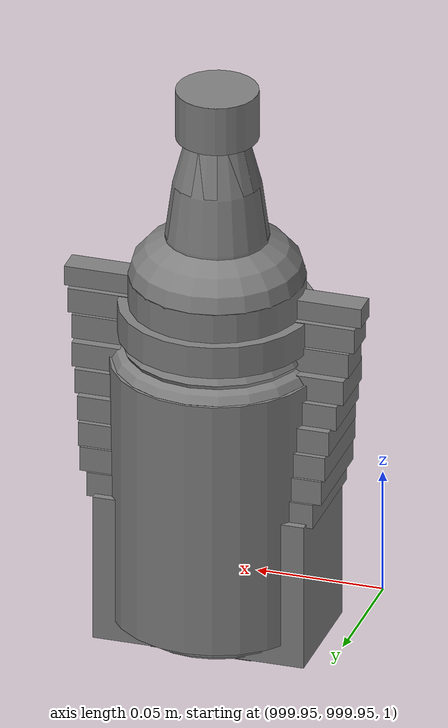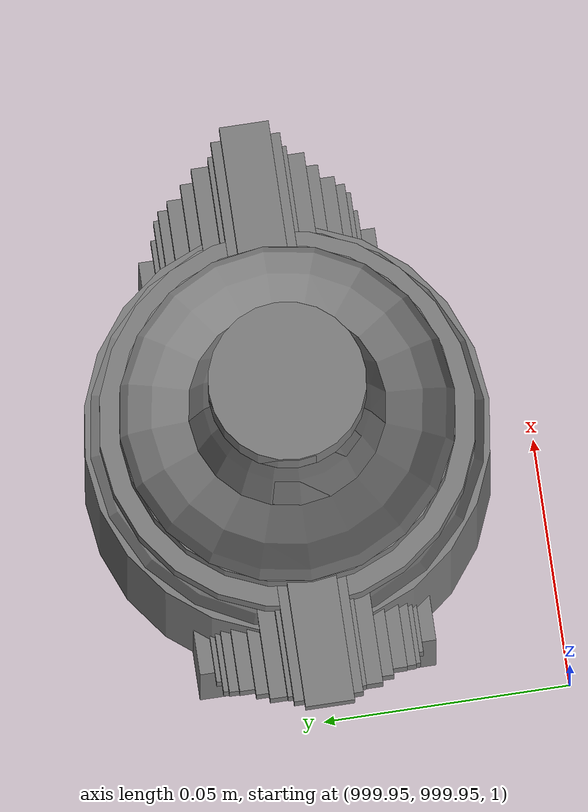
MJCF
<mujoco>
    <option gravity="0.000000000 0.000000000 -9.810000420" timestep="0.0166666" integrator="implicitfast" density="1.225" viscosity="1.8000001e-05" noslip_iterations="10" iterations="100" sdf_iterations="50">
        <flag multiccd="disable"/>
    </option>
    <size memory="1000M"/>
    <compiler coordinate="local"/>
    <worldbody>
        <light cutoff="30" pos="0 1 1" dir="0 -1 -2"/>
        <light cutoff="30" pos="0 -1 1" dir="0 1 -2"/>
        <body pos="-7.168000221 2.823999882 1.227496982" euler="-0.283413976 0.056829724 -0.133293271" name="openloong_gripper_2f85_fix_base_usda_Pos">
            <geom contype="1" conaffinity="1" density="1000" type="box" material="" rgba="0.500000000 0.500000000 0.500000000 1.000000000" solimp="0.899999976 0.949999988 0.001000000" friction="1.000000000 0.005000000 0.000100000" solref="0.020000000 1.000000000" margin="0" condim="3" group="0" pos="-0.002278805 0.074524641 -0.004134059" quat="0.315989345 0.948763072 -0.000000000 0.000000000" size="0.059999999 0.013000000 0.035000000" name="openloong_gripper_2f85_fix_base_usda_geom_F1E97FC8_5C47_4226_8BB1_711A474AB98A"/>
            <geom contype="1" conaffinity="1" density="1000" type="box" material="" rgba="0.500000000 0.500000000 0.500000000 1.000000000" solimp="0.899999976 0.949999988 0.001000000" friction="1.000000000 0.005000000 0.000100000" solref="0.020000000 1.000000000" margin="0" condim="3" group="0" pos="-0.002278805 0.078031301 0.008128285" quat="0.990447521 -0.137893379 -0.000000000 -0.000000000" size="0.059999999 0.010000000 0.035000000" name="openloong_gripper_2f85_fix_base_usda_geom_225E9049_EFD7_4AFA_839C_97F8FCA974BB"/>
            <geom contype="1" conaffinity="1" density="1000" type="box" material="" rgba="0.500000000 0.500000000 0.500000000 1.000000000" solimp="0.899999976 0.949999988 0.001000000" friction="1.000000000 0.005000000 0.000100000" solref="0.020000000 1.000000000" margin="0" condim="3" group="0" pos="-0.002278805 0.080785275 -0.002596974" quat="0.287325472 -0.957833409 0.000000000 -0.000000000" size="0.059999999 0.013000000 0.035000000" name="openloong_gripper_2f85_fix_base_usda_geom_87270E4B_823F_4A36_89BE_C0506940D6B0"/>
            <geom contype="1" conaffinity="1" density="1000" type="box" material="" rgba="0.500000000 0.500000000 0.500000000 1.000000000" solimp="0.899999976 0.949999988 0.001000000" friction="1.000000000 0.005000000 0.000100000" solref="0.020000000 1.000000000" margin="0" condim="3" group="0" pos="-0.002278805 -0.098804474 -0.020146966" quat="0.988851666 0.148906454 0.000000000 -0.000000000" size="0.059999999 0.022000000 0.020000000" name="openloong_gripper_2f85_fix_base_usda_geom_8455F81C_6CF8_4C88_89D0_5813F446715E"/>
            <geom contype="1" conaffinity="1" density="1000" type="box" material="" rgba="0.500000000 0.500000000 0.500000000 1.000000000" solimp="0.899999976 0.949999988 0.001000000" friction="1.000000000 0.005000000 0.000100000" solref="0.020000000 1.000000000" margin="0" condim="3" group="0" pos="-0.002279282 0.019920111 0.012102962" quat="0.995421767 0.095583342 -0.000000000 -0.000000000" size="0.059999999 0.025000000 0.026000001" name="openloong_gripper_2f85_fix_base_usda_geom_6832896A_9C0C_4479_9DA2_A2D588985487"/>
            <geom contype="1" conaffinity="1" density="1000" type="box" material="" rgba="0.500000000 0.500000000 0.500000000 1.000000000" solimp="0.899999976 0.949999988 0.001000000" friction="1.000000000 0.005000000 0.000100000" solref="0.020000000 1.000000000" margin="0" condim="3" group="0" pos="-0.002279282 0.005734444 -0.014276862" quat="0.999571741 -0.029275302 -0.000000000 -0.000000000" size="0.059999999 0.050000001 0.010000000" name="openloong_gripper_2f85_fix_base_usda_geom_0566F95F_49A9_4EE1_A3F1_0F9F139FA93E"/>
            <geom contype="1" conaffinity="1" density="1000" type="box" material="" rgba="0.500000000 0.500000000 0.500000000 1.000000000" solimp="0.899999976 0.949999988 0.001000000" friction="1.000000000 0.005000000 0.000100000" solref="0.020000000 1.000000000" margin="0" condim="3" group="0" pos="-0.002278805 0.079460382 0.007771969" quat="0.922590554 -0.385781586 0.000000000 -0.000000000" size="0.059999999 0.010000000 0.035000000" name="openloong_gripper_2f85_fix_base_usda_geom_482B0497_BCC5_4A50_A6E2_86B639A8C8B6"/>
            <geom contype="1" conaffinity="1" density="1000" type="box" material="" rgba="0.500000000 0.500000000 0.500000000 1.000000000" solimp="0.899999976 0.949999988 0.001000000" friction="1.000000000 0.005000000 0.000100000" solref="0.020000000 1.000000000" margin="0" condim="3" group="0" pos="-0.002279282 0.081384182 -0.001320124" quat="0.590483785 -0.807049930 0.000000000 -0.000000000" size="0.059999999 0.013000000 0.035000000" name="openloong_gripper_2f85_fix_base_usda_geom_AE96A150_307D_45B4_9B81_F0498FF9032A"/>
            <geom contype="1" conaffinity="1" density="1000" type="box" material="" rgba="0.500000000 0.500000000 0.500000000 1.000000000" solimp="0.899999976 0.949999988 0.001000000" friction="1.000000000 0.005000000 0.000100000" solref="0.020000000 1.000000000" margin="0" condim="3" group="0" pos="-0.002278805 -0.059297800 -0.007972836" quat="0.988851666 0.148906454 0.000000000 -0.000000000" size="0.059999999 0.020000000 0.022000000" name="openloong_gripper_2f85_fix_base_usda_geom_D057952C_DC8B_433D_B152_4600B0DF3B5F"/>
            <geom contype="1" conaffinity="1" density="1000" type="box" material="" rgba="0.500000000 0.500000000 0.500000000 1.000000000" solimp="0.899999976 0.949999988 0.001000000" friction="1.000000000 0.005000000 0.000100000" solref="0.020000000 1.000000000" margin="0" condim="3" group="0" pos="-0.002278805 0.076618671 -0.004656792" quat="0.004634961 0.999989629 -0.000000000 0.000000000" size="0.059999999 0.013000000 0.035000000" name="openloong_gripper_2f85_fix_base_usda_geom_2A34803F_4962_4AFD_A1B1_18EAB49C83F4"/>
            <geom contype="1" conaffinity="1" density="1000" type="box" material="" rgba="0.500000000 0.500000000 0.500000000 1.000000000" solimp="0.899999976 0.949999988 0.001000000" friction="1.000000000 0.005000000 0.000100000" solref="0.020000000 1.000000000" margin="0" condim="3" group="0" pos="-0.002279282 -0.021952629 0.002960086" quat="0.991270423 0.131847665 -0.000000000 0.000000000" size="0.059999999 0.020000000 0.024000000" name="openloong_gripper_2f85_fix_base_usda_geom_EE4E9E06_870D_4A27_B088_EEB43924EA05"/>
            <geom contype="1" conaffinity="1" density="1000" type="box" material="" rgba="0.500000000 0.500000000 0.500000000 1.000000000" solimp="0.899999976 0.949999988 0.001000000" friction="1.000000000 0.005000000 0.000100000" solref="0.020000000 1.000000000" margin="0" condim="3" group="0" pos="-0.002278805 0.081418991 0.002587914" quat="0.803492308 -0.595315695 0.000000000 -0.000000000" size="0.059999999 0.013000000 0.035000000" name="openloong_gripper_2f85_fix_base_usda_geom_F745D710_B57F_4BEE_A9A6_BDAC4CB80C4E"/>
            <geom contype="1" conaffinity="1" density="1000" type="box" material="" rgba="0.500000000 0.500000000 0.500000000 1.000000000" solimp="0.899999976 0.949999988 0.001000000" friction="1.000000000 0.005000000 0.000100000" solref="0.020000000 1.000000000" margin="0" condim="3" group="0" pos="-0.002278805 0.061115503 0.008545756" quat="0.999326169 0.036714450 0.000000000 -0.000000000" size="0.059999999 0.020000000 0.035000000" name="openloong_gripper_2f85_fix_base_usda_geom_52DD9E7F_FEC3_4A07_8A2A_3A8FB51C0C63"/>
            <freejoint name="openloong_gripper_2f85_fix_base_usda_pos_scan"/>
        </body>
        <body pos="1000.000000000 1000.000000000 1.000000000" euler="0.000000000 0.000000000 0.000000000" name="openloong_gripper_2f85_fix_base_usda_jar_01">
            <geom contype="1" conaffinity="1" density="1000" type="box" material="" rgba="0.500000000 0.500000000 0.500000000 1.000000000" solimp="0.899999976 0.949999988 0.001000000" friction="1.000000000 0.005000000 0.000100000" solref="0.020000000 1.000000000" margin="0" condim="3" group="0" pos="0.000000000 0.000000000 0.006158113" quat="1.000000000 0.000000000 0.000000000 0.000000000" size="0.020000000 0.020000000 0.005000000" name="openloong_gripper_2f85_fix_base_usda_geom_2D3E2DDF_BD3C_4737_B413_B317F0D9ADD8"/>
            <geom contype="1" conaffinity="1" density="1000" type="cylinder" material="" rgba="0.500000000 0.500000000 0.500000000 1.000000000" solimp="0.899999976 0.949999988 0.001000000" friction="1.000000000 0.005000000 0.000100000" solref="0.020000000 1.000000000" margin="0" condim="3" group="0" pos="0.000000000 0.000000000 0.062744498" quat="1.000000000 0.000000000 0.000000000 0.000000000" size="0.041000001 0.052999999 1.000000000" name="openloong_gripper_2f85_fix_base_usda_geom_A2C8AF9E_D2FC_4E03_AEB2_D2FD62D04960"/>
            <geom contype="1" conaffinity="1" density="1000" type="ellipsoid" material="" rgba="0.500000000 0.500000000 0.500000000 1.000000000" solimp="0.899999976 0.949999988 0.001000000" friction="1.000000000 0.005000000 0.000100000" solref="0.020000000 1.000000000" margin="0" condim="3" group="0" pos="0.000000000 0.000000000 0.122252703" quat="1.000000000 0.000000000 0.000000000 0.000000000" size="0.035999998 0.035999998 0.010000000" name="openloong_gripper_2f85_fix_base_usda_geom_DCEAD3DF_8D68_4A36_9C32_AC7BE387FD69"/>
            <geom contype="1" conaffinity="1" density="1000" type="cylinder" material="" rgba="0.500000000 0.500000000 0.500000000 1.000000000" solimp="0.899999976 0.949999988 0.001000000" friction="1.000000000 0.005000000 0.000100000" solref="0.020000000 1.000000000" margin="0" condim="3" group="0" pos="0.000000000 0.000000000 0.015747190" quat="1.000000000 0.000000000 0.000000000 0.000000000" size="0.035000000 0.010000000 1.000000000" name="openloong_gripper_2f85_fix_base_usda_geom_F74D7E1E_57DB_4FD1_9733_4055AB3EB491"/>
            <geom contype="1" conaffinity="1" density="1000" type="ellipsoid" material="" rgba="0.500000000 0.500000000 0.500000000 1.000000000" solimp="0.899999976 0.949999988 0.001000000" friction="1.000000000 0.005000000 0.000100000" solref="0.020000000 1.000000000" margin="0" condim="3" group="0" pos="0.000000000 0.000000000 0.115815401" quat="1.000000000 0.000000000 0.000000000 0.000000000" size="0.039999999 0.039999999 0.010000000" name="openloong_gripper_2f85_fix_base_usda_geom_8C1BA057_428C_4976_B9B3_EA34D2119681"/>
            <geom contype="1" conaffinity="1" density="1000" type="cylinder" material="" rgba="0.500000000 0.500000000 0.500000000 1.000000000" solimp="0.899999976 0.949999988 0.001000000" friction="1.000000000 0.005000000 0.000100000" solref="0.020000000 1.000000000" margin="0" condim="3" group="0" pos="0.000000000 0.000000000 0.133183479" quat="1.000000000 0.000000000 0.000000000 0.000000000" size="0.037999999 0.006500000 1.000000000" name="openloong_gripper_2f85_fix_base_usda_geom_1E69F780_A500_4984_AB71_585AD197B834"/>
            <freejoint name="openloong_gripper_2f85_fix_base_usda_jar_01_joint"/>
            <site size="0.005000000 0.005000000 0.005000000" rgba="0.500000000 0.500000000 0.500000000 1.000000000" pos="0.000000000 0.000000000 0.000000000" quat="1.000000000 0.000000000 0.000000000 0.000000000" group="0" type="sphere" name="openloong_gripper_2f85_fix_base_usda_jar_01site"/>
        </body>
        <body pos="-2.229827642 6.266748905 1.850345612" euler="-15.329902649 41.963100433 12.875673294" mocap="true" name="spotlight4_SpotLight"/>
        <body pos="-1.985090375 6.125511646 1.767473817" euler="-99.392555237 -81.172508240 25.952056885" mocap="true" name="spotlight1_SpotLight"/>
        <body pos="1000.000000000 1000.000000000 1.000000000" euler="0.000000000 0.000000000 0.000000000" name="openloong_gripper_2f85_fix_base_usda_bottle_blue">
            <geom contype="1" conaffinity="1" density="1000" type="ellipsoid" material="" rgba="0.500000000 0.500000000 0.500000000 1.000000000" solimp="0.899999976 0.949999988 0.001000000" friction="1.000000000 0.005000000 0.000100000" solref="0.020000000 1.000000000" margin="0" condim="3" group="0" pos="0.000000000 0.000000000 0.118920922" quat="1.000000000 0.000000000 0.000000000 0.000000000" size="0.030999999 0.030999999 0.029999999" name="openloong_gripper_2f85_fix_base_usda_geom_3F44D6F0_E964_43D9_A571_D58D1E2F93F9"/>
            <geom contype="1" conaffinity="1" density="1000" type="box" material="" rgba="0.500000000 0.500000000 0.500000000 1.000000000" solimp="0.899999976 0.949999988 0.001000000" friction="1.000000000 0.005000000 0.000100000" solref="0.020000000 1.000000000" margin="0" condim="3" group="0" pos="0.000000000 0.000000000 0.002164602" quat="1.000000000 0.000000000 0.000000000 0.000000000" size="0.020000000 0.020000000 0.003000000" name="openloong_gripper_2f85_fix_base_usda_geom_5C97C5AB_00FC_4194_82B3_CD34B287BA28"/>
            <geom contype="1" conaffinity="1" density="1000" type="cylinder" material="" rgba="0.500000000 0.500000000 0.500000000 1.000000000" solimp="0.899999976 0.949999988 0.001000000" friction="1.000000000 0.005000000 0.000100000" solref="0.020000000 1.000000000" margin="0" condim="3" group="0" pos="0.000000000 -0.000366211 0.060859680" quat="1.000000000 0.000000000 0.000000000 0.000000000" size="0.030999999 0.057999998 1.000000000" name="openloong_gripper_2f85_fix_base_usda_geom_A116E939_0D36_4CCE_B028_FE5333E1AC8F"/>
            <geom contype="1" conaffinity="1" density="1000" type="cylinder" material="" rgba="0.500000000 0.500000000 0.500000000 1.000000000" solimp="0.899999976 0.949999988 0.001000000" friction="1.000000000 0.005000000 0.000100000" solref="0.020000000 1.000000000" margin="0" condim="3" group="0" pos="0.000000000 0.000000000 0.220594406" quat="1.000000000 0.000000000 0.000000000 0.000000000" size="0.016000001 0.010000000 1.000000000" name="openloong_gripper_2f85_fix_base_usda_geom_F8699E81_FDE1_46C7_B3DC_72C233656301"/>
            <geom contype="1" conaffinity="1" density="1000" type="ellipsoid" material="" rgba="0.500000000 0.500000000 0.500000000 1.000000000" solimp="0.899999976 0.949999988 0.001000000" friction="1.000000000 0.005000000 0.000100000" solref="0.020000000 1.000000000" margin="0" condim="3" group="0" pos="0.000000000 0.000000000 0.144259930" quat="1.000000000 0.000000000 0.000000000 0.000000000" size="0.021000000 0.021000000 0.079999998" name="openloong_gripper_2f85_fix_base_usda_geom_586CBEB6_9411_4C09_A5A4_71D17148343E"/>
            <freejoint name="openloong_gripper_2f85_fix_base_usda_bottle_blue_joint"/>
            <site size="0.005000000 0.005000000 0.005000000" rgba="0.500000000 0.500000000 0.500000000 1.000000000" pos="0.000000000 0.000000000 0.000000000" quat="0.999961913 0.008726535 0.000000000 0.000000000" group="0" type="sphere" name="openloong_gripper_2f85_fix_base_usda_bottle_bluesite"/>
        </body>
        <body pos="1000.000000000 1000.000000000 1.000000000" euler="0.000000000 0.000000000 0.000000000" name="openloong_gripper_2f85_fix_base_usda_bottle_red">
            <geom contype="1" conaffinity="1" density="1000" type="ellipsoid" material="" rgba="0.500000000 0.500000000 0.500000000 1.000000000" solimp="0.899999976 0.949999988 0.001000000" friction="1.000000000 0.005000000 0.000100000" solref="0.020000000 1.000000000" margin="0" condim="3" group="0" pos="0.000000000 0.000000000 0.144284487" quat="1.000000000 0.000000000 0.000000000 0.000000000" size="0.021000000 0.021000000 0.079999998" name="openloong_gripper_2f85_fix_base_usda_geom_543CF9E8_5E0A_4F0B_8B36_5535E9D1F3F6"/>
            <geom contype="1" conaffinity="1" density="1000" type="cylinder" material="" rgba="0.500000000 0.500000000 0.500000000 1.000000000" solimp="0.899999976 0.949999988 0.001000000" friction="1.000000000 0.005000000 0.000100000" solref="0.020000000 1.000000000" margin="0" condim="3" group="0" pos="0.000000000 0.000000000 0.220618963" quat="1.000000000 0.000000000 0.000000000 0.000000000" size="0.016000001 0.010000000 1.000000000" name="openloong_gripper_2f85_fix_base_usda_geom_5AF3D2FF_D065_4CCC_A492_27581F6C49B7"/>
            <geom contype="1" conaffinity="1" density="1000" type="ellipsoid" material="" rgba="0.500000000 0.500000000 0.500000000 1.000000000" solimp="0.899999976 0.949999988 0.001000000" friction="1.000000000 0.005000000 0.000100000" solref="0.020000000 1.000000000" margin="0" condim="3" group="0" pos="0.000000000 0.000000000 0.118945479" quat="1.000000000 0.000000000 0.000000000 0.000000000" size="0.030999999 0.030999999 0.029999999" name="openloong_gripper_2f85_fix_base_usda_geom_51A2ECAD_D13A_49E4_8299_606D1824D109"/>
            <geom contype="1" conaffinity="1" density="1000" type="box" material="" rgba="0.500000000 0.500000000 0.500000000 1.000000000" solimp="0.899999976 0.949999988 0.001000000" friction="1.000000000 0.005000000 0.000100000" solref="0.020000000 1.000000000" margin="0" condim="3" group="0" pos="0.000000000 0.000000000 0.002189159" quat="1.000000000 0.000000000 0.000000000 0.000000000" size="0.020000000 0.020000000 0.003000000" name="openloong_gripper_2f85_fix_base_usda_geom_B148F727_6F0F_4E1B_94B0_8C6BCFCD38CD"/>
            <geom contype="1" conaffinity="1" density="1000" type="cylinder" material="" rgba="0.500000000 0.500000000 0.500000000 1.000000000" solimp="0.899999976 0.949999988 0.001000000" friction="1.000000000 0.005000000 0.000100000" solref="0.020000000 1.000000000" margin="0" condim="3" group="0" pos="0.000000000 -0.000366211 0.060884237" quat="1.000000000 0.000000000 0.000000000 0.000000000" size="0.030999999 0.057999998 1.000000000" name="openloong_gripper_2f85_fix_base_usda_geom_8614C5A7_9B8D_407D_913E_3AF8CF1BE071"/>
            <freejoint name="openloong_gripper_2f85_fix_base_usda_bottle_red_joint"/>
            <site size="0.005000000 0.005000000 0.005000000" rgba="0.500000000 0.500000000 0.500000000 1.000000000" pos="0.000000000 0.000000000 0.000000000" quat="0.999961913 0.008726535 0.000000000 0.000000000" group="0" type="sphere" name="openloong_gripper_2f85_fix_base_usda_bottle_redsite"/>
        </body>
        <body pos="1000.000000000 1000.000000000 1.000000000" euler="0.000000000 0.000000000 0.000000000" name="openloong_gripper_2f85_fix_base_usda_salt">
            <geom contype="1" conaffinity="1" density="1000" type="box" material="" rgba="0.500000000 0.500000000 0.500000000 1.000000000" solimp="0.899999976 0.949999988 0.001000000" friction="1.000000000 0.005000000 0.000100000" solref="0.020000000 1.000000000" margin="0" condim="3" group="0" pos="0.000305176 0.000000000 0.084862232" quat="1.000000000 0.000000000 0.000000000 0.000000000" size="0.048999999 0.018999999 0.005000000" name="openloong_gripper_2f85_fix_base_usda_geom_3E1BCE0F_F3DC_4D21_8231_74FA2DD4ADCB"/>
            <geom contype="1" conaffinity="1" density="1000" type="box" material="" rgba="0.500000000 0.500000000 0.500000000 1.000000000" solimp="0.899999976 0.949999988 0.001000000" friction="1.000000000 0.005000000 0.000100000" solref="0.020000000 1.000000000" margin="0" condim="3" group="0" pos="0.000305176 0.000000000 0.104564309" quat="1.000000000 0.000000000 0.000000000 0.000000000" size="0.052000001 0.014000000 0.005000000" name="openloong_gripper_2f85_fix_base_usda_geom_794C864D_9538_47D1_8E5D_150C8B039F11"/>
            <geom contype="1" conaffinity="1" density="1000" type="box" material="" rgba="0.500000000 0.500000000 0.500000000 1.000000000" solimp="0.899999976 0.949999988 0.001000000" friction="1.000000000 0.005000000 0.000100000" solref="0.020000000 1.000000000" margin="0" condim="3" group="0" pos="0.000305176 0.000000000 0.114487171" quat="1.000000000 0.000000000 0.000000000 0.000000000" size="0.054000001 0.011500000 0.005000000" name="openloong_gripper_2f85_fix_base_usda_geom_C9F824D9_5E07_4C98_B762_F03AE9AD225C"/>
            <geom contype="1" conaffinity="1" density="1000" type="box" material="" rgba="0.500000000 0.500000000 0.500000000 1.000000000" solimp="0.899999976 0.949999988 0.001000000" friction="1.000000000 0.005000000 0.000100000" solref="0.020000000 1.000000000" margin="0" condim="3" group="0" pos="0.000305176 0.000000000 0.075103164" quat="1.000000000 0.000000000 0.000000000 0.000000000" size="0.048000000 0.020000000 0.005000000" name="openloong_gripper_2f85_fix_base_usda_geom_F5E49D66_89C5_41CD_BC4D_9DF846D365B6"/>
            <geom contype="1" conaffinity="1" density="1000" type="box" material="" rgba="0.500000000 0.500000000 0.500000000 1.000000000" solimp="0.899999976 0.949999988 0.001000000" friction="1.000000000 0.005000000 0.000100000" solref="0.020000000 1.000000000" margin="0" condim="3" group="0" pos="0.000305176 0.000000000 0.134892464" quat="1.000000000 0.000000000 0.000000000 0.000000000" size="0.057000000 0.007000000 0.005000000" name="openloong_gripper_2f85_fix_base_usda_geom_293CB9A2_D6BE_43C5_B346_0C0BA366210C"/>
            <geom contype="1" conaffinity="1" density="1000" type="box" material="" rgba="0.500000000 0.500000000 0.500000000 1.000000000" solimp="0.899999976 0.949999988 0.001000000" friction="1.000000000 0.005000000 0.000100000" solref="0.020000000 1.000000000" margin="0" condim="3" group="0" pos="0.000305176 0.000000000 0.094920278" quat="1.000000000 0.000000000 0.000000000 0.000000000" size="0.050000001 0.017000001 0.005000000" name="openloong_gripper_2f85_fix_base_usda_geom_FEABB431_8D1C_41E5_AF3B_F64E304615AA"/>
            <geom contype="1" conaffinity="1" density="1000" type="box" material="" rgba="0.500000000 0.500000000 0.500000000 1.000000000" solimp="0.899999976 0.949999988 0.001000000" friction="1.000000000 0.005000000 0.000100000" solref="0.020000000 1.000000000" margin="0" condim="3" group="0" pos="0.000305176 0.000000000 0.065204859" quat="1.000000000 0.000000000 0.000000000 0.000000000" size="0.045000002 0.021000000 0.005000000" name="openloong_gripper_2f85_fix_base_usda_geom_50FA6A07_AB4E_4996_A6B9_0B4740E43DBE"/>
            <geom contype="1" conaffinity="1" density="1000" type="box" material="" rgba="0.500000000 0.500000000 0.500000000 1.000000000" solimp="0.899999976 0.949999988 0.001000000" friction="1.000000000 0.005000000 0.000100000" solref="0.020000000 1.000000000" margin="0" condim="3" group="0" pos="0.000305176 0.000000000 0.144135714" quat="1.000000000 0.000000000 0.000000000 0.000000000" size="0.059000000 0.005000000 0.004000000" name="openloong_gripper_2f85_fix_base_usda_geom_E92DDB02_646B_4FA7_BF04_1121A3ABA5BB"/>
            <geom contype="1" conaffinity="1" density="1000" type="box" material="" rgba="0.500000000 0.500000000 0.500000000 1.000000000" solimp="0.899999976 0.949999988 0.001000000" friction="1.000000000 0.005000000 0.000100000" solref="0.020000000 1.000000000" margin="0" condim="3" group="0" pos="0.000000000 0.000000000 0.031593561" quat="1.000000000 0.000000000 0.000000000 0.000000000" size="0.041999999 0.024000000 0.029999999" name="openloong_gripper_2f85_fix_base_usda_geom_4859EB3B_935C_4079_A241_944C8769A56C"/>
            <geom contype="1" conaffinity="1" density="1000" type="box" material="" rgba="0.500000000 0.500000000 0.500000000 1.000000000" solimp="0.899999976 0.949999988 0.001000000" friction="1.000000000 0.005000000 0.000100000" solref="0.020000000 1.000000000" margin="0" condim="3" group="0" pos="0.000305176 0.000000000 0.124608755" quat="1.000000000 0.000000000 0.000000000 0.000000000" size="0.055000000 0.008000000 0.005000000" name="openloong_gripper_2f85_fix_base_usda_geom_E081E294_CFA6_4EB7_8A5A_487ACBFF8532"/>
            <freejoint name="openloong_gripper_2f85_fix_base_usda_salt_joint"/>
            <site size="0.005000000 0.005000000 0.005000000" rgba="0.500000000 0.500000000 0.500000000 1.000000000" pos="0.000000000 0.000000000 0.000000000" quat="1.000000000 0.000000000 0.000000000 0.000000000" group="0" type="sphere" name="openloong_gripper_2f85_fix_base_usda_saltsite"/>
        </body>
        <body pos="-1.804379106 5.783508301 1.664561987" euler="140.021331787 -66.676834106 19.776006699" mocap="true" name="spotlight5_SpotLight"/>
        <body pos="1000.000000000 1000.000000000 1.000000000" euler="0.000000000 0.000000000 0.000000000" name="openloong_gripper_2f85_fix_base_usda_can">
            <geom contype="1" conaffinity="1" density="1000" type="cylinder" material="" rgba="0.500000000 0.500000000 0.500000000 1.000000000" solimp="0.899999976 0.949999988 0.001000000" friction="1.000000000 0.005000000 0.000100000" solref="0.020000000 1.000000000" margin="0" condim="3" group="0" pos="0.000000000 0.000000000 0.079676986" quat="1.000000000 0.000000000 0.000000000 0.000000000" size="0.034000002 0.071999997 1.000000000" name="openloong_gripper_2f85_fix_base_usda_geom_0345C2EF_AFF7_4509_985B_2AB6E0DCD770"/>
            <geom contype="1" conaffinity="1" density="1000" type="ellipsoid" material="" rgba="0.500000000 0.500000000 0.500000000 1.000000000" solimp="0.899999976 0.949999988 0.001000000" friction="1.000000000 0.005000000 0.000100000" solref="0.020000000 1.000000000" margin="0" condim="3" group="0" pos="0.000000000 0.000000000 0.151854277" quat="1.000000000 0.000000000 0.000000000 0.000000000" size="0.034000002 0.034000002 0.020000000" name="openloong_gripper_2f85_fix_base_usda_geom_295BC729_448F_4890_8C39_2482B868B7B7"/>
            <geom contype="1" conaffinity="1" density="1000" type="box" material="" rgba="0.500000000 0.500000000 0.500000000 1.000000000" solimp="0.899999976 0.949999988 0.001000000" friction="1.000000000 0.005000000 0.000100000" solref="0.020000000 1.000000000" margin="0" condim="3" group="0" pos="0.000000000 0.000000000 0.004777670" quat="1.000000000 0.000000000 0.000000000 0.000000000" size="0.020000000 0.020000000 0.005000000" name="openloong_gripper_2f85_fix_base_usda_geom_37DE5D05_C278_4893_9F20_5B487A3FA1DA"/>
            <freejoint name="openloong_gripper_2f85_fix_base_usda_can_joint"/>
            <site size="0.005000000 0.005000000 0.005000000" rgba="0.500000000 0.500000000 0.500000000 1.000000000" pos="0.000000000 0.000000000 0.000000000" quat="1.000000000 0.000000000 0.000000000 0.000000000" group="0" type="sphere" name="openloong_gripper_2f85_fix_base_usda_cansite"/>
        </body>
        <body pos="0.000000000 0.000000000 0.000000000" euler="0.000000000 0.000000000 0.000000000" name="Interactive Objects_Interactive Objects"/>
        <body pos="0.000000000 0.000000000 0.000000000" euler="0.000000000 0.000000000 0.000000000" name=" Static Objects_ Static Objects">
            <geom contype="1" conaffinity="1" density="1000" type="box" material="" rgba="0.500000000 0.500000000 0.500000000 1.000000000" solimp="0.899999976 0.949999988 0.001000000" friction="1.000000000 0.005000000 0.000100000" solref="0.020000000 1.000000000" margin="0" condim="3" group="0" pos="-6.286010742 6.153595448 1.563861728" quat="0.707107067 0.000000000 0.000000000 0.707106471" size="0.529999971 3.134999990 0.025000000" name=" Static Objects_geom_C0A93DAB_1C03_4543_BFEF_B06AD86D0887"/>
            <geom contype="1" conaffinity="1" density="1000" type="box" material="" rgba="0.500000000 0.500000000 0.500000000 1.000000000" solimp="0.899999976 0.949999988 0.001000000" friction="1.000000000 0.005000000 0.000100000" solref="0.020000000 1.000000000" margin="0" condim="3" group="0" pos="-3.101639986 6.150595188 1.018643856" quat="1.000000000 0.000000000 0.000000000 0.000000000" size="0.050000001 0.579999983 1.019999981" name=" Static Objects_geom_7E25F6DE_177C_4123_AF09_9AF7EEEFDB43"/>
            <geom contype="1" conaffinity="1" density="1000" type="box" material="" rgba="0.500000000 0.500000000 0.500000000 1.000000000" solimp="0.899999976 0.949999988 0.001000000" friction="1.000000000 0.005000000 0.000100000" solref="0.020000000 1.000000000" margin="0" condim="3" group="0" pos="-2.825197220 6.153595448 1.563861728" quat="0.707107067 0.000000000 0.000000000 0.707106471" size="0.550000012 0.239999995 0.025000000" name=" Static Objects_geom_5BDF4551_9B33_4AE3_AA42_B30187F8200B"/>
            <geom contype="1" conaffinity="1" density="1000" type="box" material="" rgba="0.500000000 0.500000000 0.500000000 1.000000000" solimp="0.899999976 0.949999988 0.001000000" friction="1.000000000 0.005000000 0.000100000" solref="0.020000000 1.000000000" margin="0" condim="3" group="0" pos="-6.311686516 6.153595448 1.018643856" quat="0.707107067 0.000000000 0.000000000 0.707106471" size="0.050000001 3.150000095 1.019999981" name=" Static Objects_geom_D4BB6695_4E59_4F0A_A119_6DBE73F5E63E"/>
            <geom contype="1" conaffinity="1" density="1000" type="box" material="" rgba="0.500000000 0.500000000 0.500000000 1.000000000" solimp="0.899999976 0.949999988 0.001000000" friction="1.000000000 0.005000000 0.000100000" solref="0.020000000 1.000000000" margin="0" condim="3" group="0" pos="-2.825197220 6.153595448 1.115278244" quat="0.707107067 0.000000000 0.000000000 0.707106471" size="0.550000012 0.239999995 0.025000000" name=" Static Objects_geom_2AD34D0B_D858_4B85_882B_C1E731C922BF"/>
            <geom contype="1" conaffinity="1" density="1000" type="box" material="" rgba="0.500000000 0.500000000 0.500000000 1.000000000" solimp="0.899999976 0.949999988 0.001000000" friction="1.000000000 0.005000000 0.000100000" solref="0.020000000 1.000000000" margin="0" condim="3" group="0" pos="-6.293097973 6.153595448 1.114443064" quat="0.707107067 0.000000000 0.000000000 0.707106471" size="0.529999971 3.134999990 0.025000000" name=" Static Objects_geom_8CDA5F94_C899_4C1F_993A_8D69C4B95683"/>
            <geom contype="1" conaffinity="1" density="1000" type="box" material="" rgba="0.500000000 0.500000000 0.500000000 1.000000000" solimp="0.899999976 0.949999988 0.001000000" friction="1.000000000 0.005000000 0.000100000" solref="0.020000000 1.000000000" margin="0" condim="3" group="0" pos="-2.825197220 6.153595448 0.629031777" quat="0.707107067 0.000000000 0.000000000 0.707106471" size="0.550000012 0.239999995 0.025000000" name=" Static Objects_geom_AA98A8F9_D8A3_42CE_AA50_C3D4960DF405"/>
            <geom contype="1" conaffinity="1" density="1000" type="box" material="" rgba="0.500000000 0.500000000 0.500000000 1.000000000" solimp="0.899999976 0.949999988 0.001000000" friction="1.000000000 0.005000000 0.000100000" solref="0.020000000 1.000000000" margin="0" condim="3" group="0" pos="-6.286010742 6.153595448 0.096129179" quat="0.707107067 0.000000000 0.000000000 0.707106471" size="0.529999971 3.134999990 0.098999999" name=" Static Objects_geom_A4688391_DF47_401F_BAB1_AC08A4516C5A"/>
            <geom contype="1" conaffinity="1" density="1000" type="box" material="" rgba="0.500000000 0.500000000 0.500000000 1.000000000" solimp="0.899999976 0.949999988 0.001000000" friction="1.000000000 0.005000000 0.000100000" solref="0.020000000 1.000000000" margin="0" condim="3" group="0" pos="-2.825197220 6.153595448 0.097434282" quat="0.707107067 0.000000000 0.000000000 0.707106471" size="0.550000012 0.239999995 0.098999999" name=" Static Objects_geom_884C0D13_BAF4_4364_8CDC_9B2D9A56907F"/>
            <geom contype="1" conaffinity="1" density="1000" type="box" material="" rgba="0.500000000 0.500000000 0.500000000 1.000000000" solimp="0.899999976 0.949999988 0.001000000" friction="1.000000000 0.005000000 0.000100000" solref="0.020000000 1.000000000" margin="0" condim="3" group="0" pos="-6.286010742 6.153595448 0.629031777" quat="0.707107067 0.000000000 0.000000000 0.707106471" size="0.529999971 3.134999990 0.025000000" name=" Static Objects_geom_0CC4101F_5055_41B7_B568_7A87DF8A7D35"/>
            <geom contype="1" conaffinity="1" density="1000" type="box" material="" rgba="0.500000000 0.500000000 0.500000000 1.000000000" solimp="0.899999976 0.949999988 0.001000000" friction="1.000000000 0.005000000 0.000100000" solref="0.020000000 1.000000000" margin="0" condim="3" group="0" pos="-6.000000000 20.159999847 2.000000000" quat="1.000000000 0.000000000 0.000000000 0.000000000" size="6.079999924 0.070000000 2.000000000" name=" Static Objects_geom_5B1C85F4_6209_4827_8B6F_F57D2D27BB7D"/>
            <geom contype="1" conaffinity="1" density="1000" type="box" material="" rgba="0.500000000 0.500000000 0.500000000 1.000000000" solimp="0.899999976 0.949999988 0.001000000" friction="1.000000000 0.005000000 0.000100000" solref="0.020000000 1.000000000" margin="0" condim="3" group="0" pos="-6.000000000 0.035000000 2.000000000" quat="1.000000000 0.000000000 0.000000000 0.000000000" size="6.079999924 0.070000000 2.000000000" name=" Static Objects_geom_FE6F27DE_FB37_4909_81BC_ED2EE3A2816E"/>
            <geom contype="1" conaffinity="1" density="1000" type="box" material="" rgba="0.500000000 0.500000000 0.500000000 1.000000000" solimp="0.899999976 0.949999988 0.001000000" friction="1.000000000 0.005000000 0.000100000" solref="0.020000000 1.000000000" margin="0" condim="3" group="0" pos="0.000000000 10.000000000 2.000000000" quat="1.000000000 0.000000000 0.000000000 0.000000000" size="0.070000000 10.500000000 2.000000000" name=" Static Objects_geom_F932AC84_ECF1_45F0_88A6_28200C2F1C6B"/>
            <geom contype="1" conaffinity="1" density="1000" type="box" material="" rgba="0.500000000 0.500000000 0.500000000 1.000000000" solimp="0.899999976 0.949999988 0.001000000" friction="1.000000000 0.005000000 0.000100000" solref="0.020000000 1.000000000" margin="0" condim="3" group="0" pos="-12.050000191 10.000000000 2.000000000" quat="1.000000000 0.000000000 0.000000000 0.000000000" size="0.070000000 10.500000000 2.000000000" name=" Static Objects_geom_EF42FDAF_A06F_428E_A100_C4A1FFF5A2D0"/>
            <geom contype="1" conaffinity="1" density="1000" type="plane" material="" rgba="0.500000000 0.500000000 0.500000000 1.000000000" solimp="0.899999976 0.949999988 0.001000000" friction="1.000000000 0.005000000 0.000100000" solref="0.020000000 1.000000000" margin="0" condim="3" group="0" pos="-6.000000000 10.399999619 0.000000000" quat="1.000000000 0.000000000 0.000000000 0.000000000" size="6.050000191 10.800000191 0.010000000" name=" Static Objects_geom_AC7512BC_A385_4F44_9BF5_F4E45139DA26"/>
            <geom contype="1" conaffinity="1" density="1000" type="box" material="" rgba="0.500000000 0.500000000 0.500000000 1.000000000" solimp="0.899999976 0.949999988 0.001000000" friction="1.000000000 0.005000000 0.000100000" solref="0.020000000 1.000000000" margin="0" condim="3" group="0" pos="-8.830721855 2.096410990 0.549305558" quat="1.000000000 0.000000000 0.000000000 0.000000000" size="0.280000001 0.430000007 0.550000012" name=" Static Objects_geom_FBC1D3E8_4439_4FF6_A3CA_B9393C35C628"/>
            <geom contype="1" conaffinity="1" density="1000" type="box" material="" rgba="0.500000000 0.500000000 0.500000000 1.000000000" solimp="0.899999976 0.949999988 0.001000000" friction="1.000000000 0.005000000 0.000100000" solref="0.020000000 1.000000000" margin="0" condim="3" group="0" pos="-6.460197449 2.937205315 0.548931718" quat="1.000000000 0.000000000 0.000000000 0.000000000" size="2.650000095 0.430000007 0.550000012" name=" Static Objects_geom_6ACBD980_DCAF_43F6_8B17_6BA0D6147159"/>
            <geom contype="1" conaffinity="1" density="1000" type="box" material="" rgba="0.500000000 0.500000000 0.500000000 1.000000000" solimp="0.899999976 0.949999988 0.001000000" friction="1.000000000 0.005000000 0.000100000" solref="0.020000000 1.000000000" margin="0" condim="3" group="0" pos="-4.240264893 1.327049494 0.549888909" quat="1.000000000 0.000000000 0.000000000 0.000000000" size="0.430000007 1.200000048 0.550000012" name=" Static Objects_geom_F1ECE445_B490_4666_989F_2AD679A9D2CB"/>
            <geom contype="1" conaffinity="1" density="1000" type="box" material="" rgba="0.500000000 0.500000000 0.500000000 1.000000000" solimp="0.899999976 0.949999988 0.001000000" friction="1.000000000 0.005000000 0.000100000" solref="0.020000000 1.000000000" margin="0" condim="3" group="0" pos="-7.408766270 3.088089943 1.776644945" quat="0.928051054 0.000000000 0.000000000 0.372453064" size="0.050000001 0.100000001 0.050000001" name=" Static Objects_geom_B3DBAE87_6501_4889_A131_A79F4FB83AD1"/>
            <geom contype="1" conaffinity="1" density="1000" type="box" material="" rgba="0.500000000 0.500000000 0.500000000 1.000000000" solimp="0.899999976 0.949999988 0.001000000" friction="1.000000000 0.005000000 0.000100000" solref="0.020000000 1.000000000" margin="0" condim="3" group="0" pos="-7.437745571 3.067511320 1.289965630" quat="1.000000000 0.000000000 0.000000000 0.000000000" size="0.029999999 0.020000000 0.020000000" name=" Static Objects_geom_9243021A_9CFF_4497_9665_48561B20E9AA"/>
            <geom contype="1" conaffinity="1" density="1000" type="box" material="" rgba="0.500000000 0.500000000 0.500000000 1.000000000" solimp="0.899999976 0.949999988 0.001000000" friction="1.000000000 0.005000000 0.000100000" solref="0.020000000 1.000000000" margin="0" condim="3" group="0" pos="-7.719123363 2.867671013 1.173410416" quat="1.000000000 0.000000000 0.000000000 0.000000000" size="0.250000000 0.250000000 0.079999998" name=" Static Objects_geom_34CFFCD7_68C4_43E7_87AA_AC1B64FBC121"/>
            <geom contype="1" conaffinity="1" density="1000" type="box" material="" rgba="0.500000000 0.500000000 0.500000000 1.000000000" solimp="0.899999976 0.949999988 0.001000000" friction="1.000000000 0.005000000 0.000100000" solref="0.020000000 1.000000000" margin="0" condim="3" group="0" pos="-7.719123363 2.958004713 1.530241251" quat="1.000000000 0.000000000 0.000000000 0.000000000" size="0.250000000 0.159999996 0.280000001" name=" Static Objects_geom_29DA339F_3014_429B_A762_CFD3396556A3"/>
            <geom contype="1" conaffinity="1" density="1000" type="cylinder" material="" rgba="0.500000000 0.500000000 0.500000000 1.000000000" solimp="0.899999976 0.949999988 0.001000000" friction="1.000000000 0.005000000 0.000100000" solref="0.020000000 1.000000000" margin="0" condim="3" group="0" pos="-7.427312374 3.069516420 1.502544641" quat="0.928051054 0.000000000 0.000000000 0.372453064" size="0.015000000 0.230000004 0.100000001" name=" Static Objects_geom_3701B391_7F98_4BF2_953B_0920322C7934"/>
            <geom contype="1" conaffinity="1" density="1000" type="box" material="" rgba="0.500000000 0.500000000 0.500000000 1.000000000" solimp="0.899999976 0.949999988 0.001000000" friction="1.000000000 0.005000000 0.000100000" solref="0.020000000 1.000000000" margin="0" condim="3" group="0" pos="-9.058088303 6.434794426 1.209077358" quat="1.000000000 0.000000000 0.000000000 0.000000000" size="0.250000000 0.100000001 0.070000000" name=" Static Objects_geom_1788BF48_EEA0_4668_8FD2_B4901D161D31"/>
            <geom contype="1" conaffinity="1" density="1000" type="box" material="" rgba="0.500000000 0.500000000 0.500000000 1.000000000" solimp="0.899999976 0.949999988 0.001000000" friction="1.000000000 0.005000000 0.000100000" solref="0.020000000 1.000000000" margin="0" condim="3" group="0" pos="-5.611940861 6.318420410 0.350975692" quat="1.000000000 0.000000000 0.000000000 0.000000000" size="0.699999988 0.100000001 0.150000006" name=" Static Objects_geom_A1443AF6_F2FC_4BD5_AEA2_120E8092E171"/>
            <geom contype="1" conaffinity="1" density="1000" type="box" material="" rgba="0.500000000 0.500000000 0.500000000 1.000000000" solimp="0.899999976 0.949999988 0.001000000" friction="1.000000000 0.005000000 0.000100000" solref="0.020000000 1.000000000" margin="0" condim="3" group="0" pos="-9.237723351 6.464855671 1.209077358" quat="1.000000000 0.000000000 0.000000000 0.000000000" size="0.100000001 0.100000001 0.070000000" name=" Static Objects_geom_F5D1DDCC_5D5E_4BE5_822E_ECC53532231D"/>
            <geom contype="1" conaffinity="1" density="1000" type="box" material="" rgba="0.500000000 0.500000000 0.500000000 1.000000000" solimp="0.899999976 0.949999988 0.001000000" friction="1.000000000 0.005000000 0.000100000" solref="0.020000000 1.000000000" margin="0" condim="3" group="0" pos="-6.300771236 6.459744930 1.744376063" quat="1.000000000 0.000000000 0.000000000 0.000000000" size="3.000000000 0.200000003 0.150000006" name=" Static Objects_geom_D21AA9E9_7BE6_46AF_A7F8_2C3F5CD0B51B"/>
            <geom contype="1" conaffinity="1" density="1000" type="box" material="" rgba="0.500000000 0.500000000 0.500000000 1.000000000" solimp="0.899999976 0.949999988 0.001000000" friction="1.000000000 0.005000000 0.000100000" solref="0.020000000 1.000000000" margin="0" condim="3" group="0" pos="-7.373087406 6.458900928 1.214329123" quat="1.000000000 0.000000000 0.000000000 0.000000000" size="0.250000000 0.200000003 0.075000003" name=" Static Objects_geom_C42EDC48_A701_4058_AD57_397D3EB22802"/>
            <geom contype="1" conaffinity="1" density="1000" type="box" material="" rgba="0.500000000 0.500000000 0.500000000 1.000000000" solimp="0.899999976 0.949999988 0.001000000" friction="1.000000000 0.005000000 0.000100000" solref="0.020000000 1.000000000" margin="0" condim="3" group="0" pos="-4.035642624 6.459744930 0.352518857" quat="1.000000000 0.000000000 0.000000000 0.000000000" size="0.800000012 0.200000003 0.150000006" name=" Static Objects_geom_06A4C7A9_CAC5_4969_BB3A_055F1FD74BFF"/>
            <geom contype="1" conaffinity="1" density="1000" type="box" material="" rgba="0.500000000 0.500000000 0.500000000 1.000000000" solimp="0.899999976 0.949999988 0.001000000" friction="1.000000000 0.005000000 0.000100000" solref="0.020000000 1.000000000" margin="0" condim="3" group="0" pos="-3.907610416 6.318625927 0.800981164" quat="1.000000000 0.000000000 0.000000000 0.000000000" size="0.500000000 0.100000001 0.150000006" name=" Static Objects_geom_0F1575B8_67D2_484B_8A19_7825F6B70631"/>
            <geom contype="1" conaffinity="1" density="1000" type="box" material="" rgba="0.500000000 0.500000000 0.500000000 1.000000000" solimp="0.899999976 0.949999988 0.001000000" friction="1.000000000 0.005000000 0.000100000" solref="0.020000000 1.000000000" margin="0" condim="3" group="0" pos="-6.098561764 6.327973843 1.292199373" quat="1.000000000 0.000000000 0.000000000 0.000000000" size="0.500000000 0.100000001 0.150000006" name=" Static Objects_geom_FBD9228A_11A9_4FA0_B6FA_95FBD0B2AF0C"/>
            <geom contype="1" conaffinity="1" density="1000" type="box" material="" rgba="0.500000000 0.500000000 0.500000000 1.000000000" solimp="0.899999976 0.949999988 0.001000000" friction="1.000000000 0.005000000 0.000100000" solref="0.020000000 1.000000000" margin="0" condim="3" group="0" pos="-7.886891365 6.459744930 0.352518857" quat="1.000000000 0.000000000 0.000000000 0.000000000" size="1.500000000 0.200000003 0.150000006" name=" Static Objects_geom_75B57A01_51D1_432E_A277_DC74770D66B9"/>
            <geom contype="1" conaffinity="1" density="1000" type="box" material="" rgba="0.500000000 0.500000000 0.500000000 1.000000000" solimp="0.899999976 0.949999988 0.001000000" friction="1.000000000 0.005000000 0.000100000" solref="0.020000000 1.000000000" margin="0" condim="3" group="0" pos="-6.824534416 6.447464466 1.212718010" quat="1.000000000 0.000000000 0.000000000 0.000000000" size="0.100000001 0.100000001 0.075000003" name=" Static Objects_geom_96A9440D_0BC6_43DF_A7D4_AD352B201B00"/>
            <geom contype="1" conaffinity="1" density="1000" type="box" material="" rgba="0.500000000 0.500000000 0.500000000 1.000000000" solimp="0.899999976 0.949999988 0.001000000" friction="1.000000000 0.005000000 0.000100000" solref="0.020000000 1.000000000" margin="0" condim="3" group="0" pos="-4.407354832 6.459744930 1.292199373" quat="1.000000000 0.000000000 0.000000000 0.000000000" size="1.240000010 0.200000003 0.150000006" name=" Static Objects_geom_A1326840_EA4E_4E59_9944_BEC505322819"/>
            <geom contype="1" conaffinity="1" density="1000" type="box" material="" rgba="0.500000000 0.500000000 0.500000000 1.000000000" solimp="0.899999976 0.949999988 0.001000000" friction="1.000000000 0.005000000 0.000100000" solref="0.020000000 1.000000000" margin="0" condim="3" group="0" pos="-6.751636982 6.459744930 0.800981164" quat="1.000000000 0.000000000 0.000000000 0.000000000" size="2.200000048 0.200000003 0.150000006" name=" Static Objects_geom_6D7781AD_D14B_4947_B2B0_88B5CD3D2CE4"/>
            <geom contype="1" conaffinity="1" density="1000" type="box" material="" rgba="0.500000000 0.500000000 0.500000000 1.000000000" solimp="0.899999976 0.949999988 0.001000000" friction="1.000000000 0.005000000 0.000100000" solref="0.020000000 1.000000000" margin="0" condim="3" group="0" pos="-6.924745083 6.362090111 1.214329123" quat="1.000000000 0.000000000 0.000000000 0.000000000" size="0.200000003 0.100000001 0.075000003" name=" Static Objects_geom_24F75C92_BB6F_4864_8F7E_4A98A1EE15C1"/>
            <geom contype="1" conaffinity="1" density="1000" type="box" material="" rgba="0.500000000 0.500000000 0.500000000 1.000000000" solimp="0.899999976 0.949999988 0.001000000" friction="1.000000000 0.005000000 0.000100000" solref="0.020000000 1.000000000" margin="0" condim="3" group="0" pos="-8.844120979 6.464855671 1.209077358" quat="1.000000000 0.000000000 0.000000000 0.000000000" size="0.100000001 0.100000001 0.070000000" name=" Static Objects_geom_B8CBAA9A_7BBC_4CEC_BBCB_9A7F6B22B46E"/>
            <geom contype="1" conaffinity="1" density="1000" type="box" material="" rgba="0.500000000 0.500000000 0.500000000 1.000000000" solimp="0.899999976 0.949999988 0.001000000" friction="1.000000000 0.005000000 0.000100000" solref="0.020000000 1.000000000" margin="0" condim="3" group="0" pos="-3.157672644 6.136868477 1.348373055" quat="1.000000000 0.000000000 0.000000000 0.000000000" size="0.200000003 0.519999981 0.300000012" name=" Static Objects_geom_5609D611_5F36_4803_8228_85C62113AC83"/>
        </body>
        <body pos="-6.332345009 2.779978037 1.034067392" euler="0.000000000 0.000000000 0.000000000" name="openloong_gripper_2f85_fix_base_usda_basket">
            <geom contype="1" conaffinity="1" density="100000" type="box" material="" rgba="0.500000000 0.500000000 0.500000000 1.000000000" solimp="0.899999976 0.949999988 0.001000000" friction="1.000000000 0.899999976 0.000100000" solref="0.020000000 1.000000000" margin="0" condim="3" group="0" pos="-0.039724827 -0.188568115 0.167089701" quat="0.997537494 0.070135131 0.000000000 0.000000000" size="0.150000006 0.006000000 0.108000003" name="openloong_gripper_2f85_fix_base_usda_geom_E719AB25_4312_41CC_8945_4996BFBD5627"/>
            <geom contype="1" conaffinity="1" density="100000" type="box" material="" rgba="0.500000000 0.500000000 0.500000000 1.000000000" solimp="0.899999976 0.949999988 0.001000000" friction="1.000000000 0.899999976 0.000100000" solref="0.020000000 1.000000000" margin="0" condim="3" group="0" pos="0.094372749 0.000000000 0.168361664" quat="0.706172049 0.036353335 0.036353379 0.706171215" size="0.200000003 0.006000000 0.108000003" name="openloong_gripper_2f85_fix_base_usda_geom_D756F663_D083_4CF3_92AA_6C34F13719AE"/>
            <geom contype="1" conaffinity="1" density="100000" type="box" material="" rgba="0.500000000 0.500000000 0.500000000 1.000000000" solimp="0.899999976 0.949999988 0.001000000" friction="1.000000000 0.899999976 0.000100000" solref="0.020000000 1.000000000" margin="0" condim="3" group="0" pos="-0.039724827 0.000000000 0.068126202" quat="1.000000000 0.000000000 0.000000000 0.000000000" size="0.129999995 0.174999997 0.006000000" name="openloong_gripper_2f85_fix_base_usda_geom_A8B544F2_7B99_4A8C_9447_60AC6F6E6620"/>
            <geom contype="1" conaffinity="1" density="100000" type="box" material="" rgba="0.500000000 0.500000000 0.500000000 1.000000000" solimp="0.899999976 0.949999988 0.001000000" friction="1.000000000 0.899999976 0.000100000" solref="0.020000000 1.000000000" margin="0" condim="3" group="0" pos="-0.039724827 0.188377380 0.167089701" quat="0.997489929 -0.070808925 0.000000000 0.000000000" size="0.150000006 0.006000000 0.108000003" name="openloong_gripper_2f85_fix_base_usda_geom_35EFDAFA_8DE9_48C0_BD51_79DAC76EFE56"/>
            <geom contype="1" conaffinity="1" density="100000" type="box" material="" rgba="0.500000000 0.500000000 0.500000000 1.000000000" solimp="0.899999976 0.949999988 0.001000000" friction="1.000000000 0.899999976 0.000100000" solref="0.020000000 1.000000000" margin="0" condim="3" group="0" pos="-0.172339439 0.000000000 0.168361664" quat="0.706172407 -0.036353018 -0.036353093 0.706170976" size="0.200000003 0.006000000 0.108000003" name="openloong_gripper_2f85_fix_base_usda_geom_E0409FFF_6EE0_4E13_9675_95D93293AE76"/>
            <freejoint name="openloong_gripper_2f85_fix_base_usda_basket_joint"/>
            <site size="0.005000000 0.005000000 0.005000000" rgba="0.500000000 0.500000000 0.500000000 1.000000000" pos="0.000000000 0.000000000 0.000000000" quat="1.000000000 0.000000000 0.000000000 0.000000000" group="0" type="sphere" name="openloong_gripper_2f85_fix_base_usda_basketsite"/>
        </body>
        <body pos="-3.510578632 3.403555870 -0.000000100" euler="0.000000000 0.000000000 40.200675964" name="openloong_gripper_2f85_fix_base_usda_PZ">
            <geom contype="1" conaffinity="1" density="1000" type="box" material="" rgba="0.500000000 0.500000000 0.500000000 1.000000000" solimp="0.899999976 0.949999988 0.001000000" friction="1.000000000 0.005000000 0.000100000" solref="0.020000000 1.000000000" margin="0" condim="3" group="0" pos="-0.047453165 0.056484699 0.373715430" quat="0.934750080 0.077914521 0.028795123 0.345459938" size="0.180000007 0.010000000 0.379999995" name="openloong_gripper_2f85_fix_base_usda_geom_DCD4DEF1_842A_48B8_9978_9DD8C23AC569"/>
            <geom contype="1" conaffinity="1" density="1000" type="box" material="" rgba="0.500000000 0.500000000 0.500000000 1.000000000" solimp="0.899999976 0.949999988 0.001000000" friction="1.000000000 0.005000000 0.000100000" solref="0.020000000 1.000000000" margin="0" condim="3" group="0" pos="0.047452450 -0.054376602 0.374072611" quat="0.934387863 -0.082143910 -0.030358355 0.345326364" size="0.180000007 0.010000000 0.379999995" name="openloong_gripper_2f85_fix_base_usda_geom_3F0D8C15_786C_4757_A446_271D2F083195"/>
            <freejoint name="openloong_gripper_2f85_fix_base_usda_PZ"/>
        </body>
        <body pos="-2.436573029 6.404376507 0.137849092" euler="0.000000000 0.000000000 0.000000000" name="openloong_gripper_2f85_fix_base_usda_shoppingtrolley_01">
            <geom contype="1" conaffinity="1" density="1000" type="box" material="" rgba="0.500000000 0.500000000 0.500000000 1.000000000" solimp="0.899999976 0.949999988 0.001000000" friction="1.000000000 0.005000000 0.000100000" solref="0.020000000 1.000000000" margin="0" condim="3" group="0" pos="-0.107458733 0.238907143 0.911498845" quat="0.634576976 0.622505128 -0.330067992 -0.317575932" size="0.017999999 0.022499999 0.035999998" name="openloong_gripper_2f85_fix_base_usda_geom_D2262C73_AF07_4EDE_9800_292A59C4AAF1"/>
            <geom contype="1" conaffinity="1" density="1000" type="box" material="" rgba="0.500000000 0.500000000 0.500000000 1.000000000" solimp="0.899999976 0.949999988 0.001000000" friction="1.000000000 0.005000000 0.000100000" solref="0.020000000 1.000000000" margin="0" condim="3" group="0" pos="-0.126757339 -0.182533979 0.598989725" quat="0.996607184 0.055331606 -0.059003651 -0.015205891" size="0.013499999 0.287999988 0.053999998" name="openloong_gripper_2f85_fix_base_usda_geom_36F292D7_5AAA_4F84_8FFC_29AF22B97D9B"/>
            <geom contype="1" conaffinity="1" density="1000" type="box" material="" rgba="0.500000000 0.500000000 0.500000000 1.000000000" solimp="0.899999976 0.949999988 0.001000000" friction="1.000000000 0.005000000 0.000100000" solref="0.020000000 1.000000000" margin="0" condim="3" group="0" pos="-0.005004787 0.248085022 0.912686050" quat="1.000000000 0.000000000 0.000000000 0.000000000" size="0.107999995 0.022499999 0.022499999" name="openloong_gripper_2f85_fix_base_usda_geom_F25B3D6E_FDC6_4797_B9F0_21F05AFE9BF0"/>
            <geom contype="1" conaffinity="1" density="1000" type="box" material="" rgba="0.500000000 0.500000000 0.500000000 1.000000000" solimp="0.899999976 0.949999988 0.001000000" friction="1.000000000 0.005000000 0.000100000" solref="0.020000000 1.000000000" margin="0" condim="3" group="0" pos="-0.169898406 -0.043119621 0.915120542" quat="0.687021017 0.726584017 -0.005590606 -0.006832919" size="0.017999999 0.022499999 0.089999996" name="openloong_gripper_2f85_fix_base_usda_geom_ECCD595A_ACC4_4038_A2C6_0610F5BAC709"/>
            <geom contype="1" conaffinity="1" density="1000" type="box" material="" rgba="0.500000000 0.500000000 0.500000000 1.000000000" solimp="0.899999976 0.949999988 0.001000000" friction="1.000000000 0.005000000 0.000100000" solref="0.020000000 1.000000000" margin="0" condim="3" group="0" pos="0.148195267 -0.199506566 0.782808602" quat="0.998808920 0.017156634 0.026950166 0.036880098" size="0.013499999 0.305999994 0.063000001" name="openloong_gripper_2f85_fix_base_usda_geom_C4674D33_58A7_4395_BC3D_1DFE546E5680"/>
            <geom contype="1" conaffinity="1" density="1000" type="box" material="" rgba="0.500000000 0.500000000 0.500000000 1.000000000" solimp="0.899999976 0.949999988 0.001000000" friction="1.000000000 0.005000000 0.000100000" solref="0.020000000 1.000000000" margin="0" condim="3" group="0" pos="-0.142927840 -0.199506134 0.784674108" quat="0.998421252 0.016904408 -0.027109101 -0.046199299" size="0.013499999 0.305999994 0.063000001" name="openloong_gripper_2f85_fix_base_usda_geom_530FBF37_DD69_4CBC_949C_2D76332B1E97"/>
            <geom contype="1" conaffinity="1" density="1000" type="box" material="" rgba="0.500000000 0.500000000 0.500000000 1.000000000" solimp="0.899999976 0.949999988 0.001000000" friction="1.000000000 0.005000000 0.000100000" solref="0.020000000 1.000000000" margin="0" condim="3" group="0" pos="-0.000004721 -0.174527690 0.560063601" quat="0.996704638 0.081116498 -0.000000004 0.000000000" size="0.126000002 0.287999988 0.009000000" name="openloong_gripper_2f85_fix_base_usda_geom_AA7911F2_18B2_4799_8ADD_83A71509A751"/>
            <geom contype="1" conaffinity="1" density="1000" type="box" material="" rgba="0.500000000 0.500000000 0.500000000 1.000000000" solimp="0.899999976 0.949999988 0.001000000" friction="1.000000000 0.005000000 0.000100000" solref="0.020000000 1.000000000" margin="0" condim="3" group="0" pos="-0.160832763 0.103427693 0.910528183" quat="0.711469591 0.699786782 -0.048386075 -0.042050660" size="0.017999999 0.022499999 0.071999997" name="openloong_gripper_2f85_fix_base_usda_geom_EA6F68E4_F4FF_4DE3_B3BA_3671DF67BA7B"/>
            <geom contype="1" conaffinity="1" density="1000" type="box" material="" rgba="0.500000000 0.500000000 0.500000000 1.000000000" solimp="0.899999976 0.949999988 0.001000000" friction="1.000000000 0.005000000 0.000100000" solref="0.020000000 1.000000000" margin="0" condim="3" group="0" pos="-0.169898406 -0.178061336 0.864131629" quat="0.916343808 -0.400392294 -0.000000045 0.000000030" size="0.017999999 0.022499999 0.089999996" name="openloong_gripper_2f85_fix_base_usda_geom_7A52A64B_EF8C_4040_A328_47DC28CF744F"/>
            <geom contype="1" conaffinity="1" density="1000" type="box" material="" rgba="0.500000000 0.500000000 0.500000000 1.000000000" solimp="0.899999976 0.949999988 0.001000000" friction="1.000000000 0.005000000 0.000100000" solref="0.020000000 1.000000000" margin="0" condim="3" group="0" pos="-0.000006008 -0.484932661 0.670727849" quat="0.997585475 0.069449045 -0.000000004 -0.000000089" size="0.179999992 0.013499999 0.170999989" name="openloong_gripper_2f85_fix_base_usda_geom_E646D6F4_111B_4330_A8FA_51315A71A57A"/>
            <geom contype="1" conaffinity="1" density="1000" type="box" material="" rgba="0.500000000 0.500000000 0.500000000 1.000000000" solimp="0.899999976 0.949999988 0.001000000" friction="1.000000000 0.005000000 0.000100000" solref="0.020000000 1.000000000" margin="0" condim="3" group="0" pos="0.134013891 0.200098798 0.912192523" quat="0.692574680 -0.680924535 -0.166899428 0.169783980" size="0.017999999 0.022499999 0.035999998" name="openloong_gripper_2f85_fix_base_usda_geom_FDF3122E_C33F_4824_B923_6E0CA2D3B852"/>
            <geom contype="1" conaffinity="1" density="1000" type="box" material="" rgba="0.500000000 0.500000000 0.500000000 1.000000000" solimp="0.899999976 0.949999988 0.001000000" friction="1.000000000 0.005000000 0.000100000" solref="0.020000000 1.000000000" margin="0" condim="3" group="0" pos="0.141839072 -0.191051379 0.702451229" quat="0.997147262 0.056065105 0.045779929 0.021407485" size="0.013499999 0.287999988 0.053999998" name="openloong_gripper_2f85_fix_base_usda_geom_4A661AB6_86F2_44C2_ABB2_E09F4037620C"/>
            <geom contype="1" conaffinity="1" density="1000" type="box" material="" rgba="0.500000000 0.500000000 0.500000000 1.000000000" solimp="0.899999976 0.949999988 0.001000000" friction="1.000000000 0.005000000 0.000100000" solref="0.020000000 1.000000000" margin="0" condim="3" group="0" pos="0.169898629 -0.178061336 0.864131629" quat="0.916343808 -0.400392294 -0.000000045 0.000000030" size="0.017999999 0.022499999 0.089999996" name="openloong_gripper_2f85_fix_base_usda_geom_06447217_CCCC_4632_9145_6C27668A0447"/>
            <geom contype="1" conaffinity="1" density="1000" type="box" material="" rgba="0.500000000 0.500000000 0.500000000 1.000000000" solimp="0.899999976 0.949999988 0.001000000" friction="1.000000000 0.005000000 0.000100000" solref="0.020000000 1.000000000" margin="0" condim="3" group="0" pos="-0.000005364 0.100332208 0.734785020" quat="0.999668717 0.025737956 -0.000000010 0.000000000" size="0.135000005 0.019800000 0.152999997" name="openloong_gripper_2f85_fix_base_usda_geom_9624E7C2_A4D3_48CB_9091_2A654D147C74"/>
            <geom contype="1" conaffinity="1" density="1000" type="box" material="" rgba="0.500000000 0.500000000 0.500000000 1.000000000" solimp="0.899999976 0.949999988 0.001000000" friction="1.000000000 0.005000000 0.000100000" solref="0.020000000 1.000000000" margin="0" condim="3" group="0" pos="-0.012634277 -0.174527690 -0.088243507" quat="1.000000000 0.000000000 -0.000000004 0.000000000" size="0.135000005 0.287999988 0.044999998" name="openloong_gripper_2f85_fix_base_usda_geom_9DC83389_A8A3_41E9_AA81_DE8F02D69A6C"/>
            <geom contype="1" conaffinity="1" density="1000" type="box" material="" rgba="0.500000000 0.500000000 0.500000000 1.000000000" solimp="0.899999976 0.949999988 0.001000000" friction="1.000000000 0.005000000 0.000100000" solref="0.020000000 1.000000000" margin="0" condim="3" group="0" pos="0.131482959 -0.182533979 0.598989725" quat="0.996607125 0.055331629 0.059003670 0.015205893" size="0.013499999 0.287999988 0.053999998" name="openloong_gripper_2f85_fix_base_usda_geom_68C474E1_C970_4AC0_9BFB_127C2753C034"/>
            <geom contype="1" conaffinity="1" density="1000" type="box" material="" rgba="0.500000000 0.500000000 0.500000000 1.000000000" solimp="0.899999976 0.949999988 0.001000000" friction="1.000000000 0.005000000 0.000100000" solref="0.020000000 1.000000000" margin="0" condim="3" group="0" pos="0.103667587 0.233050480 0.912927270" quat="0.634205043 -0.622199059 -0.324503720 0.324576139" size="0.017999999 0.022499999 0.035999998" name="openloong_gripper_2f85_fix_base_usda_geom_A4CA344B_AB0E_430C_B449_502902159618"/>
            <geom contype="1" conaffinity="1" density="1000" type="box" material="" rgba="0.500000000 0.500000000 0.500000000 1.000000000" solimp="0.899999976 0.949999988 0.001000000" friction="1.000000000 0.005000000 0.000100000" solref="0.020000000 1.000000000" margin="0" condim="3" group="0" pos="-0.134013891 0.200098798 0.912192523" quat="0.694057047 0.679413557 -0.172947660 -0.163618833" size="0.017999999 0.022499999 0.035999998" name="openloong_gripper_2f85_fix_base_usda_geom_AB091846_B766_4F58_BC09_A679DD77F914"/>
            <geom contype="1" conaffinity="1" density="1000" type="box" material="" rgba="0.500000000 0.500000000 0.500000000 1.000000000" solimp="0.899999976 0.949999988 0.001000000" friction="1.000000000 0.005000000 0.000100000" solref="0.020000000 1.000000000" margin="0" condim="3" group="0" pos="-0.135714188 -0.191051379 0.694841146" quat="0.997147322 0.056064609 -0.045779683 -0.021407485" size="0.013499999 0.287999988 0.053999998" name="openloong_gripper_2f85_fix_base_usda_geom_75D28680_B7C5_4F85_9B5B_004F04059C77"/>
            <geom contype="1" conaffinity="1" density="1000" type="box" material="" rgba="0.500000000 0.500000000 0.500000000 1.000000000" solimp="0.899999976 0.949999988 0.001000000" friction="1.000000000 0.005000000 0.000100000" solref="0.020000000 1.000000000" margin="0" condim="3" group="0" pos="0.169898629 -0.043119621 0.915120542" quat="0.687029123 -0.726576388 -0.006509603 0.005963952" size="0.017999999 0.022499999 0.089999996" name="openloong_gripper_2f85_fix_base_usda_geom_3E1AEBE6_4668_4287_A12D_90EC2CA66594"/>
            <geom contype="1" conaffinity="1" density="1000" type="box" material="" rgba="0.500000000 0.500000000 0.500000000 1.000000000" solimp="0.899999976 0.949999988 0.001000000" friction="1.000000000 0.005000000 0.000100000" solref="0.020000000 1.000000000" margin="0" condim="3" group="0" pos="0.160832971 0.103427693 0.910528183" quat="0.711112797 -0.700149298 -0.042821646 0.047705106" size="0.017999999 0.022499999 0.071999997" name="openloong_gripper_2f85_fix_base_usda_geom_9E0891B3_05C3_4BF9_A913_636FCA61B1AB"/>
            <freejoint name="openloong_gripper_2f85_fix_base_usda_shoppingtrolley_01_joint"/>
            <site size="0.005000000 0.005000000 0.005000000" rgba="0.500000000 0.500000000 0.500000000 1.000000000" pos="0.000000000 0.000000000 0.000000000" quat="1.000000000 0.000000000 0.000000000 0.000000000" group="0" type="sphere" name="openloong_gripper_2f85_fix_base_usda_shoppingtrolley_01"/>
        </body>
        <body pos="-2.162922621 6.180304527 -0.123990871" euler="0.000000000 0.000000000 180.000000000" mocap="true" name="openloong_gripper_2f85_fix_base_usda_leftHandMocap"/>
        <body pos="-2.162922621 6.180304527 -0.123990871" euler="0.000000000 0.000000000 180.000000000" mocap="true" name="openloong_gripper_2f85_fix_base_usda_rightHandMocap"/>
        <body pos="-2.162922621 6.180304527 1.076009154" euler="0.000000000 0.000000000 180.000000000" name="openloong_gripper_2f85_fix_base_usda_base_link">
            <geom contype="1" conaffinity="1" density="1000" type="mesh" material="" rgba="0.783999979 0.783999979 0.783999979 1.000000000" solimp="0.899999976 0.949999988 0.001000000" friction="1.000000000 0.005000000 0.000100000" solref="0.020000000 1.000000000" margin="0" condim="3" group="3" mesh="base_link" pos="0.000000000 0.000000000 0.000000000" quat="1.000000000 0.000000000 0.000000000 0.000000000" size="1.000000000 1.000000000 1.000000000" name="openloong_gripper_2f85_fix_base_usda__geom_7_A4B616F0_DF45_4EFF_81C2_653AADF42A7C"/>
            <site size="0.005000000 0.005000000 0.005000000" rgba="0.500000000 0.500000000 0.500000000 1.000000000" pos="0.000000000 0.000000000 0.000000000" quat="1.000000000 0.000000000 0.000000000 0.000000000" group="0" type="sphere" name="openloong_gripper_2f85_fix_base_usda_imu"/>
            <inertial mass="22.447001" pos="-0.005664100 -0.001336700 0.238289997" diaginertia="0.374352545 0.277180195 0.220617250" quat="0.999247074 0.035235517 -0.015086859 0.006023135"/>
            <body pos="0.000000000 0.000000000 0.300000072" euler="0.000000000 0.000000000 0.000000000" name="openloong_gripper_2f85_fix_base_usda_dummy_body">
                <geom contype="1" conaffinity="1" density="1000" type="sphere" material="" rgba="0.783999979 0.783999979 0.783999979 1.000000000" solimp="0.899999976 0.949999988 0.001000000" friction="1.000000000 0.005000000 0.000100000" solref="0.020000000 1.000000000" margin="0" condim="3" group="3" pos="0.000000000 0.000000000 0.000000000" quat="1.000000000 0.000000000 0.000000000 0.000000000" size="0.010000000 0.000000000 0.000000000" name="openloong_gripper_2f85_fix_base_usda__geom_8_DD8A0E85_AFB5_45A5_A848_B13C48108759"/>
                <joint armature="0.0099999998" stiffness="0" damping="0.1" axis="0.000000 0.000000 1.000000" type="hinge" name="openloong_gripper_2f85_fix_base_usda_dummy_joint"/>
                <site size="0.010000000 0.005000000 0.005000000" rgba="0.500000000 0.500000000 0.500000000 1.000000000" pos="0.000000000 0.000000000 0.000000000" quat="1.000000000 0.000000000 0.000000000 0.000000000" group="3" type="sphere" name="openloong_gripper_2f85_fix_base_usda_dummy_site"/>
            </body>
            <body pos="0.009000063 0.000000000 0.406399965" euler="0.000000000 0.000000000 0.000000000" name="openloong_gripper_2f85_fix_base_usda_Link_head_yaw">
                <geom contype="1" conaffinity="1" density="1000" type="mesh" material="" rgba="0.783999979 0.783999979 0.783999979 1.000000000" solimp="0.899999976 0.949999988 0.001000000" friction="1.000000000 0.005000000 0.000100000" solref="0.020000000 1.000000000" margin="0" condim="3" group="3" mesh="Link_head_yaw" pos="0.000000000 0.000000000 0.000000000" quat="1.000000000 0.000000000 0.000000000 0.000000000" size="1.000000000 1.000000000 1.000000000" name="openloong_gripper_2f85_fix_base_usda__geom_10_F82DAFB4_655A_4626_9E4B_7421E90858B4"/>
                <inertial mass="0.84249002" pos="0.000000000 -0.002081400 0.044801001" diaginertia="0.000700588 0.000629000 0.000553812" quat="0.706933022 -0.015675601 0.015677100 0.706933022"/>
                <body pos="0.000000000 -0.034599781 0.048499942" euler="0.000000000 0.000000000 0.000000000" name="openloong_gripper_2f85_fix_base_usda_Link_head_pitch">
                    <geom contype="1" conaffinity="1" density="1000" type="mesh" material="" rgba="0.783999979 0.783999979 0.783999979 1.000000000" solimp="0.899999976 0.949999988 0.001000000" friction="1.000000000 0.005000000 0.000100000" solref="0.020000000 1.000000000" margin="0" condim="3" group="3" mesh="Link_head_pitch" pos="0.000000000 0.000000000 0.000000000" quat="1.000000000 0.000000000 0.000000000 0.000000000" size="1.000000000 1.000000000 1.000000000" name="openloong_gripper_2f85_fix_base_usda__geom_12_4D5A9015_4497_45D2_AF54_C99D1A10F78D"/>
                    <inertial mass="1.3943" pos="0.020569000 0.033004001 0.125000000" diaginertia="0.006381400 0.006289940 0.004481460" quat="0.973390222 0.008406822 0.228157058 0.019624906"/>
                    <body pos="0.000000000 0.030000210 0.000000000" euler="0.000000000 0.000000000 0.000000000" name="openloong_gripper_2f85_fix_base_usda_neck_center_body">
                        <site size="0.010000000 0.005000000 0.005000000" rgba="0.500000000 0.500000000 0.500000000 1.000000000" pos="0.000000000 0.000000000 0.000000000" quat="1.000000000 0.000000000 0.000000000 0.000000000" group="3" type="sphere" name="openloong_gripper_2f85_fix_base_usda_neck_center_site"/>
                        <body pos="0.019999981 0.000000000 0.149999976" euler="-0.000002229 39.998176575 -90.000205994" name="openloong_gripper_2f85_fix_base_usda_camera_head">
                            <site size="0.010000000 0.005000000 0.005000000" rgba="0.500000000 0.500000000 0.500000000 1.000000000" pos="0.000000000 0.000000000 0.000000000" quat="1.000000000 0.000000000 0.000000000 0.000000000" group="3" type="sphere" name="openloong_gripper_2f85_fix_base_usda_camera_head_site"/>
                        </body>
                    </body>
                </body>
            </body>
            <body pos="0.003999949 -0.161600113 0.392199993" euler="0.000000000 0.000000000 0.000000000" name="openloong_gripper_2f85_fix_base_usda_Link_arm_r_01">
                <geom contype="1" conaffinity="1" density="1000" type="mesh" material="" rgba="0.783999979 0.783999979 0.783999979 1.000000000" solimp="0.899999976 0.949999988 0.001000000" friction="1.000000000 0.005000000 0.000100000" solref="0.020000000 1.000000000" margin="0" condim="3" group="3" mesh="Link_arm_r_01" pos="0.000000000 0.000000000 0.000000000" quat="1.000000000 0.000000000 0.000000000 0.000000000" size="1.000000000 1.000000000 1.000000000" name="openloong_gripper_2f85_fix_base_usda__geom_14_7745EA1F_33E7_4768_B446_73365D781585"/>
                <joint armature="0.0099999998" stiffness="0" damping="1" axis="0.000000 -1.000000 0.000000" limited="true" range="-170.000015259 170.000015259" type="hinge" name="openloong_gripper_2f85_fix_base_usda_J_arm_r_01"/>
                <inertial mass="0.75641" pos="0.004494600 -0.038293999 -0.000001874" diaginertia="0.000842990 0.000803050 0.000587120" quat="-0.000163502 0.707098067 0.000812463 0.707115054"/>
                <body pos="-0.042000055 -0.040999889 0.000000000" euler="0.000000000 0.000000000 0.000000000" name="openloong_gripper_2f85_fix_base_usda_Link_arm_r_02">
                    <geom contype="1" conaffinity="1" density="1000" type="mesh" material="" rgba="0.783999979 0.783999979 0.783999979 1.000000000" solimp="0.899999976 0.949999988 0.001000000" friction="1.000000000 0.005000000 0.000100000" solref="0.020000000 1.000000000" margin="0" condim="3" group="3" mesh="Link_arm_r_02" pos="0.000000000 0.000000000 0.000000000" quat="1.000000000 0.000000000 0.000000000 0.000000000" size="1.000000000 1.000000000 1.000000000" name="openloong_gripper_2f85_fix_base_usda__geom_16_329D58A5_8FBB_4617_8260_3AA288A24DEB"/>
                    <joint armature="0.0099999998" stiffness="0" damping="1" axis="-1.000000 0.000000 0.000000" limited="true" range="-105.000244141 105.000244141" type="hinge" name="openloong_gripper_2f85_fix_base_usda_J_arm_r_02"/>
                    <inertial mass="0.98500001" pos="0.041999999 -0.067430697 0.000000000" diaginertia="0.002262690 0.001730990 0.001154020" quat="0.500000000 0.500000000 -0.500000000 0.500000000"/>
                    <body pos="0.042000055 -0.122600079 0.000000000" euler="0.000000000 0.000000000 0.000000000" name="openloong_gripper_2f85_fix_base_usda_Link_arm_r_03">
                        <geom contype="1" conaffinity="1" density="1000" type="mesh" material="" rgba="0.783999979 0.783999979 0.783999979 1.000000000" solimp="0.899999976 0.949999988 0.001000000" friction="1.000000000 0.005000000 0.000100000" solref="0.020000000 1.000000000" margin="0" condim="3" group="3" mesh="Link_arm_r_03" pos="0.000000000 0.000000000 0.000000000" quat="1.000000000 0.000000000 0.000000000 0.000000000" size="1.000000000 1.000000000 1.000000000" name="openloong_gripper_2f85_fix_base_usda__geom_18_04CD02C6_95C8_414D_BB0A_893CBA76BADD"/>
                        <joint armature="0.0099999998" stiffness="0" damping="1" axis="0.000000 -1.000000 0.000000" limited="true" range="-170.000015259 170.000015259" type="hinge" name="openloong_gripper_2f85_fix_base_usda_J_arm_r_03"/>
                        <inertial mass="0.95899999" pos="-0.001413580 -0.164663002 0.020757901" diaginertia="0.002101340 0.002064590 0.000754802" quat="0.560480952 0.454391927 -0.443732947 0.531497955"/>
                        <body pos="0.035300016 -0.177400112 0.024000049" euler="0.000000000 0.000000000 0.000000000" name="openloong_gripper_2f85_fix_base_usda_Link_arm_r_04">
                            <geom contype="1" conaffinity="1" density="1000" type="mesh" material="" rgba="0.783999979 0.783999979 0.783999979 1.000000000" solimp="0.899999976 0.949999988 0.001000000" friction="1.000000000 0.005000000 0.000100000" solref="0.020000000 1.000000000" margin="0" condim="3" group="3" mesh="Link_arm_r_04" pos="0.000000000 0.000000000 0.000000000" quat="1.000000000 0.000000000 0.000000000 0.000000000" size="1.000000000 1.000000000 1.000000000" name="openloong_gripper_2f85_fix_base_usda__geom_20_59956C02_106E_4B25_AF44_B3E482CA7980"/>
                            <joint armature="0.0099999998" stiffness="0" damping="1" axis="-1.000000 0.000000 0.000000" limited="true" range="0.000000000 170.000015259" type="hinge" name="openloong_gripper_2f85_fix_base_usda_J_arm_r_04"/>
                            <inertial mass="0.60000002" pos="-0.038727000 -0.060766999 -0.021003000" diaginertia="0.001092610 0.000712422 0.000645102" quat="0.327701002 0.632602990 -0.467366993 0.523443997"/>
                            <body pos="-0.035300016 -0.103499889 -0.024000049" euler="0.000000000 0.000000000 0.000000000" name="openloong_gripper_2f85_fix_base_usda_Link_arm_r_05">
                                <geom contype="1" conaffinity="1" density="1000" type="mesh" material="" rgba="0.783999979 0.783999979 0.783999979 1.000000000" solimp="0.899999976 0.949999988 0.001000000" friction="1.000000000 0.005000000 0.000100000" solref="0.020000000 1.000000000" margin="0" condim="3" group="3" mesh="Link_arm_r_05" pos="0.000000000 0.000000000 0.000000000" quat="1.000000000 0.000000000 0.000000000 0.000000000" size="1.000000000 1.000000000 1.000000000" name="openloong_gripper_2f85_fix_base_usda__geom_22_35394691_0942_4E4A_BA60_7BF2AEA56ED5"/>
                                <joint armature="0.0099999998" stiffness="0" damping="1" axis="0.000000 -1.000000 0.000000" limited="true" range="-170.000015259 170.000015259" type="hinge" name="openloong_gripper_2f85_fix_base_usda_J_arm_r_05"/>
                                <inertial mass="0.68976003" pos="0.000032712 -0.068658002 -0.000111780" diaginertia="0.002522510 0.002411100 0.000448695" quat="0.707660973 0.706543028 -0.002603360 0.002470550"/>
                                <body pos="-0.026499987 -0.196499825 0.000000000" euler="0.000000000 0.000000000 0.000000000" name="openloong_gripper_2f85_fix_base_usda_Link_arm_r_06">
                                    <geom contype="1" conaffinity="1" density="1000" type="mesh" material="" rgba="0.783999979 0.783999979 0.783999979 1.000000000" solimp="0.899999976 0.949999988 0.001000000" friction="1.000000000 0.005000000 0.000100000" solref="0.020000000 1.000000000" margin="0" condim="3" group="3" mesh="Link_arm_r_06" pos="0.000000000 0.000000000 0.000000000" quat="1.000000000 0.000000000 0.000000000 0.000000000" size="1.000000000 1.000000000 1.000000000" name="openloong_gripper_2f85_fix_base_usda__geom_24_FB0D3C2F_36CD_4FA7_9B59_A4F429435498"/>
                                    <joint armature="0.0099999998" stiffness="0" damping="1" axis="1.000000 0.000000 0.000000" limited="true" range="-105.000244141 105.000244141" type="hinge" name="openloong_gripper_2f85_fix_base_usda_J_arm_r_06"/>
                                    <inertial mass="0.28" pos="0.026078001 -0.000000896 0.001663700" diaginertia="0.000156930 0.000145601 0.000104979" quat="0.707080841 0.001851080 0.001883810 0.707127810"/>
                                    <body pos="0.026499987 0.000000000 0.031800032" euler="0.000000000 0.000000000 0.000000000" name="openloong_gripper_2f85_fix_base_usda_Link_arm_r_07">
                                        <geom contype="1" conaffinity="1" density="1000" type="mesh" material="" rgba="0.783999979 0.783999979 0.783999979 1.000000000" solimp="0.899999976 0.949999988 0.001000000" friction="1.000000000 0.005000000 0.000100000" solref="0.020000000 1.000000000" margin="0" condim="3" group="3" mesh="Link_arm_r_07" pos="0.000000000 0.000000000 0.000000000" quat="1.000000000 0.000000000 0.000000000 0.000000000" size="1.000000000 1.000000000 1.000000000" name="openloong_gripper_2f85_fix_base_usda__geom_26_96A70D93_10D1_4F9D_95F7_4EE73D88BA32"/>
                                        <joint armature="0.0099999998" stiffness="0" damping="1" axis="0.000000 0.000000 1.000000" limited="true" range="-60.000133514 60.000133514" type="hinge" name="openloong_gripper_2f85_fix_base_usda_J_arm_r_07"/>
                                        <inertial mass="0.61353999" pos="-0.007859000 -0.158170000 -0.027736001" diaginertia="0.003037610 0.002570910 0.000729379" quat="0.427542925 0.443532884 -0.553093910 0.560867906"/>
                                        <body pos="0.000000000 0.287000179 -0.269999981" euler="150.000350952 0.000000000 0.000000000" name="openloong_gripper_2f85_fix_base_usda_camera_wrist_r">
                                            <site size="0.010000000 0.005000000 0.005000000" rgba="0.500000000 0.500000000 0.500000000 1.000000000" pos="0.000000000 0.000000000 0.000000000" quat="1.000000000 0.000000000 0.000000000 0.000000000" group="3" type="sphere" name="openloong_gripper_2f85_fix_base_usda_camera_wrist_r_site"/>
                                        </body>
                                        <body pos="0.000000000 -0.219999790 -0.032999992" euler="0.000000000 0.000000000 179.999969482" name="openloong_gripper_2f85_fix_base_usda_ee_center_body_r">
                                            <site size="0.010000000 0.005000000 0.005000000" rgba="0.500000000 0.500000000 0.500000000 1.000000000" pos="0.000000000 0.000000000 0.000000000" quat="1.000000000 0.000000000 0.000000000 0.000000000" group="3" type="sphere" name="openloong_gripper_2f85_fix_base_usda_ee_center_site_r"/>
                                        </body>
                                        <body pos="0.000000000 -0.065999985 -0.031000018" euler="89.999984741 0.000000000 180.000000000" name="openloong_gripper_2f85_fix_base_usda_zbr_base_link">
                                            <geom contype="1" conaffinity="1" density="1000" type="mesh" material="" rgba="0.783999979 0.783999979 0.783999979 1.000000000" solimp="0.899999976 0.949999988 0.001000000" friction="1.000000000 0.005000000 0.000100000" solref="0.020000000 1.000000000" margin="0" condim="3" group="3" mesh="base" pos="0.000000000 0.000000000 0.000000000" quat="1.000000000 0.000000000 0.000000000 0.000000000" size="1.000000238 1.000000238 1.000000238" name="openloong_gripper_2f85_fix_base_usda__geom_30_4D5AF700_4CC5_4118_85D0_082E369761D5"/>
                                            <inertial mass="0.77744102" pos="0.000000000 -0.000027039 0.035467502" diaginertia="0.000260285 0.000225381 0.000152708" quat="0.999998808 -0.001528488 0.000000000 0.000000000"/>
                                            <body pos="-0.030601032 0.004750133 0.065703884" euler="-89.999977112 0.000000000 0.000000000" name="openloong_gripper_2f85_fix_base_usda_r_left_driver">
                                                <geom contype="1" conaffinity="1" density="1000" type="mesh" material="" rgba="0.783999979 0.783999979 0.783999979 1.000000000" solimp="0.899999976 0.949999988 0.001000000" friction="1.000000000 0.005000000 0.000100000" solref="0.020000000 1.000000000" margin="0" condim="3" group="3" mesh="driver" pos="0.030601032 0.054904476 -0.004699946" quat="0.707106709 0.707106590 0.000000000 0.000000000" size="1.000000238 1.000000238 1.000000238" name="openloong_gripper_2f85_fix_base_usda__geom_32_69C98BC0_47C9_4533_984A_DA97A2692216"/>
                                                <joint armature="0.0049999999" stiffness="0" damping="0.1" axis="0.000000 0.000000 1.000000" limited="true" range="0.000000000 51.566200256" type="hinge" name="openloong_gripper_2f85_fix_base_usda_r_left_driver_joint"/>
                                                <inertial mass="0.0089956298" pos="0.000000000 0.017754700 0.001073140" diaginertia="0.000001724 0.000001609 0.000000322" quat="0.681301236 0.732003212 0.000000000 0.000000000"/>
                                                <body pos="-0.031425007 0.004532338 -0.010200026" euler="0.000000000 0.000000000 180.000000000" name="openloong_gripper_2f85_fix_base_usda_r_left_coupler">
                                                    <geom contype="1" conaffinity="1" density="1000" type="mesh" material="" rgba="0.783999979 0.783999979 0.783999979 1.000000000" solimp="0.899999976 0.949999988 0.001000000" friction="1.000000000 0.005000000 0.000100000" solref="0.020000000 1.000000000" margin="0" condim="3" group="3" mesh="coupler" pos="-0.062026039 -0.050372135 0.005499960" quat="0.707106709 -0.707106590 0.000000000 0.000000000" size="1.000000238 1.000000238 1.000000238" name="openloong_gripper_2f85_fix_base_usda__geom_34_C8BBC084_71B4_423B_9F91_B4A1CF8766CB"/>
                                                    <inertial mass="0.0140974" pos="0.000000000 0.003012090 0.023217499" diaginertia="0.000004162 0.000003522 0.000000888" quat="0.705635548 -0.045590367 0.045590367 0.705635548"/>
                                                </body>
                                            </body>
                                            <body pos="-0.012700084 -0.011999848 0.072219387" euler="-89.999977112 0.000000000 0.000000000" name="openloong_gripper_2f85_fix_base_usda_r_left_spring_link">
                                                <geom contype="1" conaffinity="1" density="1000" type="mesh" material="" rgba="0.783999979 0.783999979 0.783999979 1.000000000" solimp="0.899999976 0.949999988 0.001000000" friction="1.000000000 0.005000000 0.000100000" solref="0.020000000 1.000000000" margin="0" condim="3" group="3" mesh="spring_link" pos="0.012700084 0.061419979 0.012050035" quat="0.707106709 0.707106590 0.000000000 0.000000000" size="1.000000238 1.000000238 1.000000238" name="openloong_gripper_2f85_fix_base_usda__geom_36_03AD3E85_7E04_4DF5_BFAF_DC5EDA7AAF95"/>
                                                <joint armature="0.001" stiffness="0.050000001" damping="0.00125" axis="0.000000 0.000000 1.000000" limited="true" range="-17.000000000 51.566200256" type="hinge" name="openloong_gripper_2f85_fix_base_usda_r_left_spring_link_joint"/>
                                                <inertial mass="0.0221642" pos="-0.000000009 0.018162400 0.021265799" diaginertia="0.000008969 0.000006717 0.000002639" quat="0.663403213 -0.244737089 0.244737089 0.663403213"/>
                                                <body pos="-0.038208015 -0.042500507 0.002949954" euler="180.000000000 0.000000000 -0.002179886" name="openloong_gripper_2f85_fix_base_usda_r_left_follower">
                                                    <geom contype="1" conaffinity="1" density="1000" type="mesh" material="" rgba="0.783999979 0.783999979 0.783999979 1.000000000" solimp="0.899999976 0.949999988 0.001000000" friction="1.000000000 0.005000000 0.000100000" solref="0.020000000 1.000000000" margin="0" condim="3" group="3" mesh="follower" pos="0.050907861 -0.103920005 -0.009100081" quat="0.707106709 -0.707106590 0.000000000 -0.000000000" size="1.000000238 1.000000238 1.000000238" name="openloong_gripper_2f85_fix_base_usda__geom_39_84C8AD91_270A_4F09_8B95_BFFB3490BB40"/>
                                                    <geom contype="1" conaffinity="1" density="1000" type="mesh" material="" rgba="0.783999979 0.783999979 0.783999979 1.000000000" solimp="0.899999976 0.949999988 0.001000000" friction="1.000000000 0.005000000 0.000100000" solref="0.020000000 1.000000000" margin="0" condim="3" group="3" mesh="tongue" pos="0.050907861 -0.103920005 -0.009100081" quat="0.707106709 -0.707106590 0.000000000 -0.000000000" size="1.000000238 1.000000238 1.000000238" name="openloong_gripper_2f85_fix_base_usda__geom_40_F576FBC3_BEDC_4249_BA7E_C0F63C268EAD"/>
                                                    <joint armature="0.001" stiffness="0" damping="0.1" axis="0.000000 0.000000 1.000000" limited="true" range="-49.999961853 51.566200256" type="hinge" name="openloong_gripper_2f85_fix_base_usda_r_left_follower"/>
                                                    <inertial mass="0.0125222" pos="0.000000000 -0.011046000 0.012478600" diaginertia="0.000002674 0.000002456 0.000000602" quat="0.986436546 0.164143041 0.000000000 0.000000000"/>
                                                    <body pos="-0.037789829 -0.103916191 -0.009100081" euler="-89.999961853 0.000000000 -0.000000000" name="openloong_gripper_2f85_fix_base_usda_r_left_pad">
                                                        <geom contype="1" conaffinity="1" density="1000" type="box" material="" rgba="0.449999988 0.449999988 0.449999988 1.000000000" solimp="0.949999988 0.990000010 0.001000000" friction="0.600000024 0.005000000 0.000100000" solref="0.020000000 1.000000000" margin="0" condim="3" group="3" mass="1e-06" pos="0.043257724 -0.000000119 0.138749629" quat="0.999999821 0.000000000 0.000000000 0.000000000" size="0.002000001 0.011000003 0.009375002" name="openloong_gripper_2f85_fix_base_usda_r_left_pad2_D62A5A51_D70A_4CD2_AD95_EADA09DD98B0"/>
                                                        <geom contype="1" conaffinity="1" density="1000" type="box" material="" rgba="0.550000012 0.550000012 0.550000012 1.000000000" solimp="0.949999988 0.990000010 0.001000000" friction="0.699999988 0.005000000 0.000100000" solref="0.020000000 1.000000000" margin="0" condim="3" group="3" mass="1e-06" pos="0.043257724 -0.000000119 0.120000392" quat="0.999999821 0.000000000 0.000000000 0.000000000" size="0.002000001 0.011000003 0.009375002" name="openloong_gripper_2f85_fix_base_usda_r_left_pad1_2AF84CB8_2B4F_4093_8E5A_BC6234B2AC02"/>
                                                    </body>
                                                </body>
                                            </body>
                                            <body pos="0.030601032 -0.004749895 0.065703884" euler="89.999984741 0.000000000 180.000000000" name="openloong_gripper_2f85_fix_base_usda_r_right_driver">
                                                <geom contype="1" conaffinity="1" density="1000" type="mesh" material="" rgba="0.783999979 0.783999979 0.783999979 1.000000000" solimp="0.899999976 0.949999988 0.001000000" friction="1.000000000 0.005000000 0.000100000" solref="0.020000000 1.000000000" margin="0" condim="3" group="3" mesh="driver" pos="0.030601032 0.054904476 -0.004699946" quat="0.707106829 0.707106709 0.000000000 0.000000000" size="1.000000238 1.000000238 1.000000238" name="openloong_gripper_2f85_fix_base_usda__geom_42_041C3904_3266_415B_BD0E_3C171E8AB9B9"/>
                                                <joint armature="0.0049999999" stiffness="0" damping="0.1" axis="0.000000 0.000000 1.000000" limited="true" range="0.000000000 51.566200256" type="hinge" name="openloong_gripper_2f85_fix_base_usda_r_right_driver_joint"/>
                                                <inertial mass="0.0089956298" pos="0.000000000 0.017754700 0.001073140" diaginertia="0.000001724 0.000001609 0.000000322" quat="0.681301236 0.732003212 0.000000000 0.000000000"/>
                                                <body pos="-0.031425007 0.004532338 -0.010200026" euler="0.000000000 0.000000000 180.000000000" name="openloong_gripper_2f85_fix_base_usda_r_right_coupler">
                                                    <geom contype="1" conaffinity="1" density="1000" type="mesh" material="" rgba="0.783999979 0.783999979 0.783999979 1.000000000" solimp="0.899999976 0.949999988 0.001000000" friction="1.000000000 0.005000000 0.000100000" solref="0.020000000 1.000000000" margin="0" condim="3" group="3" mesh="coupler" pos="-0.062026039 -0.050372135 0.005499960" quat="0.707106829 -0.707106709 0.000000000 0.000000000" size="1.000000238 1.000000238 1.000000238" name="openloong_gripper_2f85_fix_base_usda__geom_44_53C504CF_A4F5_4428_BD5A_F2D0839AB523"/>
                                                    <inertial mass="0.0140974" pos="0.000000000 0.003012090 0.023217499" diaginertia="0.000004162 0.000003522 0.000000888" quat="0.705635548 -0.045590367 0.045590367 0.705635548"/>
                                                </body>
                                            </body>
                                            <body pos="0.012700084 0.012000087 0.072219387" euler="89.999984741 0.000000000 180.000000000" name="openloong_gripper_2f85_fix_base_usda_r_right_spring_link">
                                                <geom contype="1" conaffinity="1" density="1000" type="mesh" material="" rgba="0.783999979 0.783999979 0.783999979 1.000000000" solimp="0.899999976 0.949999988 0.001000000" friction="1.000000000 0.005000000 0.000100000" solref="0.020000000 1.000000000" margin="0" condim="3" group="3" mesh="spring_link" pos="0.012700084 0.061419979 0.012050035" quat="0.707106829 0.707106709 0.000000000 0.000000000" size="1.000000238 1.000000238 1.000000238" name="openloong_gripper_2f85_fix_base_usda__geom_46_D498407B_5BA8_4B61_9CBA_F53C12C300C0"/>
                                                <joint armature="0.001" stiffness="0.050000001" damping="0.00125" axis="0.000000 0.000000 1.000000" limited="true" range="-17.000000000 51.566200256" type="hinge" name="openloong_gripper_2f85_fix_base_usda_r_right_spring_link_joint"/>
                                                <inertial mass="0.0221642" pos="-0.000000009 0.018162400 0.021265799" diaginertia="0.000008969 0.000006717 0.000002639" quat="0.663403213 -0.244737089 0.244737089 0.663403213"/>
                                                <body pos="-0.038208015 -0.042500507 0.002949954" euler="180.000000000 0.000000000 0.000000000" name="openloong_gripper_2f85_fix_base_usda_r_right_follower">
                                                    <geom contype="1" conaffinity="1" density="1000" type="mesh" material="" rgba="0.783999979 0.783999979 0.783999979 1.000000000" solimp="0.899999976 0.949999988 0.001000000" friction="1.000000000 0.005000000 0.000100000" solref="0.020000000 1.000000000" margin="0" condim="3" group="3" mesh="follower" pos="0.050907861 -0.103920005 -0.009099962" quat="0.707106829 -0.707106709 0.000000000 0.000000000" size="1.000000238 1.000000238 1.000000238" name="openloong_gripper_2f85_fix_base_usda__geom_50_E5DEAAD6_8391_44E3_93DB_9A5F164C864B"/>
                                                    <geom contype="1" conaffinity="1" density="1000" type="mesh" material="" rgba="0.783999979 0.783999979 0.783999979 1.000000000" solimp="0.899999976 0.949999988 0.001000000" friction="1.000000000 0.005000000 0.000100000" solref="0.020000000 1.000000000" margin="0" condim="3" group="3" mesh="tongue" pos="0.050907861 -0.103920005 -0.009099962" quat="0.707106829 -0.707106709 0.000000000 0.000000000" size="1.000000238 1.000000238 1.000000238" name="openloong_gripper_2f85_fix_base_usda__geom_49_82619A99_81B1_4D79_98B2_123F0A9318E3"/>
                                                    <joint armature="0.001" stiffness="0" damping="0.1" axis="0.000000 0.000000 1.000000" limited="true" range="-49.999961853 51.566200256" type="hinge" name="openloong_gripper_2f85_fix_base_usda_r_right_follower_joint"/>
                                                    <inertial mass="0.0125222" pos="0.000000000 -0.011046000 0.012478600" diaginertia="0.000002674 0.000002456 0.000000602" quat="0.986436546 0.164143041 0.000000000 0.000000000"/>
                                                    <body pos="-0.037789829 -0.103916191 -0.009099962" euler="-89.999984741 0.000000000 0.000000000" name="openloong_gripper_2f85_fix_base_usda_r_right_pad">
                                                        <geom contype="1" conaffinity="1" density="1000" type="box" material="" rgba="0.550000012 0.550000012 0.550000012 1.000000000" solimp="0.949999988 0.990000010 0.001000000" friction="0.699999988 0.005000000 0.000100000" solref="0.020000000 1.000000000" margin="0" condim="3" group="3" mass="1e-06" pos="0.043257963 -0.000000596 0.119998962" quat="1.000000000 0.000000000 0.000000000 0.000000000" size="0.002000001 0.011000003 0.009375002" name="openloong_gripper_2f85_fix_base_usda_r_right_pad1_0F0A51A3_6713_4A0A_BA43_DB4F6CDB5FDB"/>
                                                        <geom contype="1" conaffinity="1" density="1000" type="box" material="" rgba="0.449999988 0.449999988 0.449999988 1.000000000" solimp="0.949999988 0.990000010 0.001000000" friction="0.600000024 0.005000000 0.000100000" solref="0.020000000 1.000000000" margin="0" condim="3" group="3" mass="1e-06" pos="0.043257963 -0.000000596 0.138749152" quat="1.000000000 0.000000000 0.000000000 0.000000000" size="0.002000001 0.011000003 0.009375002" name="openloong_gripper_2f85_fix_base_usda_r_right_pad2_BBB48A3A_F755_4A9F_AC14_AF3535862313"/>
                                                    </body>
                                                </body>
                                            </body>
                                        </body>
                                    </body>
                                </body>
                            </body>
                        </body>
                    </body>
                </body>
            </body>
            <body pos="0.003999949 0.161600113 0.392199993" euler="0.000000000 0.000000000 0.000000000" name="openloong_gripper_2f85_fix_base_usda_Link_arm_l_01">
                <geom contype="1" conaffinity="1" density="1000" type="mesh" material="" rgba="0.783999979 0.783999979 0.783999979 1.000000000" solimp="0.899999976 0.949999988 0.001000000" friction="1.000000000 0.005000000 0.000100000" solref="0.020000000 1.000000000" margin="0" condim="3" group="3" mesh="Link_arm_l_01" pos="0.000000000 0.000000000 0.000000000" quat="1.000000000 0.000000000 0.000000000 0.000000000" size="1.000000000 1.000000000 1.000000000" name="openloong_gripper_2f85_fix_base_usda__geom_52_62416A44_BBAA_46DC_804A_9086D984EF31"/>
                <joint armature="0.0099999998" stiffness="0" damping="1" axis="0.000000 1.000000 0.000000" limited="true" range="-170.000015259 170.000015259" type="hinge" name="openloong_gripper_2f85_fix_base_usda_J_arm_l_01"/>
                <inertial mass="0.75640601" pos="-0.004494650 0.038294200 -0.000001874" diaginertia="0.000842986 0.000803053 0.000587115" quat="-0.000812496 0.707115054 0.000163424 0.707098067"/>
                <body pos="0.042000055 0.040999889 0.000000000" euler="0.000000000 0.000000000 0.000000000" name="openloong_gripper_2f85_fix_base_usda_Link_arm_l_02">
                    <geom contype="1" conaffinity="1" density="1000" type="mesh" material="" rgba="0.783999979 0.783999979 0.783999979 1.000000000" solimp="0.899999976 0.949999988 0.001000000" friction="1.000000000 0.005000000 0.000100000" solref="0.020000000 1.000000000" margin="0" condim="3" group="3" mesh="Link_arm_l_02" pos="0.000000000 0.000000000 0.000000000" quat="1.000000000 0.000000000 0.000000000 0.000000000" size="1.000000000 1.000000000 1.000000000" name="openloong_gripper_2f85_fix_base_usda__geom_54_9943646D_0C0D_44D5_B6C0_8B1F12BBE110"/>
                    <joint armature="0.0099999998" stiffness="0" damping="1" axis="-1.000000 0.000000 0.000000" limited="true" range="-105.000244141 105.000244141" type="hinge" name="openloong_gripper_2f85_fix_base_usda_J_arm_l_02"/>
                    <inertial mass="0.98500001" pos="-0.041999999 0.067430697 0.000000000" diaginertia="0.002262690 0.001730990 0.001154020" quat="0.500000000 0.500000000 -0.500000000 0.500000000"/>
                    <body pos="-0.042000055 0.122600079 0.000000000" euler="0.000000000 0.000000000 0.000000000" name="openloong_gripper_2f85_fix_base_usda_Link_arm_l_03">
                        <geom contype="1" conaffinity="1" density="1000" type="mesh" material="" rgba="0.783999979 0.783999979 0.783999979 1.000000000" solimp="0.899999976 0.949999988 0.001000000" friction="1.000000000 0.005000000 0.000100000" solref="0.020000000 1.000000000" margin="0" condim="3" group="3" mesh="Link_arm_l_03" pos="0.000000000 0.000000000 0.000000000" quat="1.000000000 0.000000000 0.000000000 0.000000000" size="1.000000000 1.000000000 1.000000000" name="openloong_gripper_2f85_fix_base_usda__geom_56_24B96A39_199D_4159_9ED0_CC5CF1CD7A67"/>
                        <joint armature="0.0099999998" stiffness="0" damping="1" axis="0.000000 1.000000 0.000000" limited="true" range="-170.000015259 170.000015259" type="hinge" name="openloong_gripper_2f85_fix_base_usda_J_arm_l_03"/>
                        <inertial mass="0.95899999" pos="0.001413580 0.164663002 0.020757901" diaginertia="0.002101340 0.002064590 0.000754802" quat="0.443732947 0.531497955 -0.560480952 0.454391927"/>
                        <body pos="-0.035300016 0.177400112 0.024000049" euler="0.000000000 0.000000000 0.000000000" name="openloong_gripper_2f85_fix_base_usda_Link_arm_l_04">
                            <geom contype="1" conaffinity="1" density="1000" type="mesh" material="" rgba="0.783999979 0.783999979 0.783999979 1.000000000" solimp="0.899999976 0.949999988 0.001000000" friction="1.000000000 0.005000000 0.000100000" solref="0.020000000 1.000000000" margin="0" condim="3" group="3" mesh="Link_arm_l_04" pos="0.000000000 0.000000000 0.000000000" quat="1.000000000 0.000000000 0.000000000 0.000000000" size="1.000000000 1.000000000 1.000000000" name="openloong_gripper_2f85_fix_base_usda__geom_58_7997F7E8_A4A9_49BE_925B_443158FA66AC"/>
                            <joint armature="0.0099999998" stiffness="0" damping="1" axis="1.000000 0.000000 0.000000" limited="true" range="0.000000000 170.000015259" type="hinge" name="openloong_gripper_2f85_fix_base_usda_J_arm_l_04"/>
                            <inertial mass="0.60000002" pos="0.038727000 0.060767200 -0.021003200" diaginertia="0.001092570 0.000712419 0.000645098" quat="0.467370987 0.523440003 -0.327692002 0.632607996"/>
                            <body pos="0.035300016 0.103499889 -0.024000049" euler="0.000000000 0.000000000 0.000000000" name="openloong_gripper_2f85_fix_base_usda_Link_arm_l_05">
                                <geom contype="1" conaffinity="1" density="1000" type="mesh" material="" rgba="0.783999979 0.783999979 0.783999979 1.000000000" solimp="0.899999976 0.949999988 0.001000000" friction="1.000000000 0.005000000 0.000100000" solref="0.020000000 1.000000000" margin="0" condim="3" group="3" mesh="Link_arm_l_05" pos="0.000000000 0.000000000 0.000000000" quat="1.000000000 0.000000000 0.000000000 0.000000000" size="1.000000000 1.000000000 1.000000000" name="openloong_gripper_2f85_fix_base_usda__geom_60_825333D7_D88D_448E_87E1_A265265F50F3"/>
                                <joint armature="0.0099999998" stiffness="0" damping="1" axis="0.000000 1.000000 0.000000" limited="true" range="-170.000015259 170.000015259" type="hinge" name="openloong_gripper_2f85_fix_base_usda_J_arm_l_05"/>
                                <inertial mass="0.68976003" pos="-0.000032712 0.068658002 -0.000111780" diaginertia="0.002522510 0.002411100 0.000448695" quat="0.706543028 0.707660973 0.002470550 -0.002603360"/>
                                <body pos="0.026499987 0.196499825 0.000000000" euler="0.000000000 0.000000000 0.000000000" name="openloong_gripper_2f85_fix_base_usda_Link_arm_l_06">
                                    <geom contype="1" conaffinity="1" density="1000" type="mesh" material="" rgba="0.783999979 0.783999979 0.783999979 1.000000000" solimp="0.899999976 0.949999988 0.001000000" friction="1.000000000 0.005000000 0.000100000" solref="0.020000000 1.000000000" margin="0" condim="3" group="3" mesh="Link_arm_l_06" pos="0.000000000 0.000000000 0.000000000" quat="1.000000000 0.000000000 0.000000000 0.000000000" size="1.000000000 1.000000000 1.000000000" name="openloong_gripper_2f85_fix_base_usda__geom_62_9F56B7EE_A273_47FF_87FA_74D29CF4ABDE"/>
                                    <joint armature="0.0099999998" stiffness="0" damping="1" axis="-1.000000 0.000000 0.000000" limited="true" range="-105.000244141 105.000244141" type="hinge" name="openloong_gripper_2f85_fix_base_usda_J_arm_l_06"/>
                                    <inertial mass="0.28" pos="-0.026077701 0.000000896 0.001663730" diaginertia="0.000156927 0.000145598 0.000104981" quat="0.707080841 -0.001851280 -0.001884020 0.707127810"/>
                                    <body pos="-0.026499987 0.000000000 0.031800032" euler="0.000000000 0.000000000 0.000000000" name="openloong_gripper_2f85_fix_base_usda_Link_arm_l_07">
                                        <geom contype="1" conaffinity="1" density="1000" type="mesh" material="" rgba="0.783999979 0.783999979 0.783999979 1.000000000" solimp="0.899999976 0.949999988 0.001000000" friction="1.000000000 0.005000000 0.000100000" solref="0.020000000 1.000000000" margin="0" condim="3" group="3" mesh="Link_arm_l_07" pos="0.000000000 0.000000000 0.000000000" quat="1.000000000 0.000000000 0.000000000 0.000000000" size="1.000000000 1.000000000 1.000000000" name="openloong_gripper_2f85_fix_base_usda__geom_64_1CE40032_8E5B_4C56_BE47_0C12B2F2CA6C"/>
                                        <joint armature="0.0099999998" stiffness="0" damping="1" axis="0.000000 0.000000 1.000000" limited="true" range="-60.000133514 60.000133514" type="hinge" name="openloong_gripper_2f85_fix_base_usda_J_arm_l_07"/>
                                        <inertial mass="0.61353999" pos="-0.007787200 0.157049999 -0.027733000" diaginertia="0.003037200 0.002570420 0.000729374" quat="0.443562120 0.427539080 -0.560871124 0.553070128"/>
                                        <body pos="0.000000000 -0.287000179 -0.269999981" euler="-150.000350952 -0.000000001 179.976669312" name="openloong_gripper_2f85_fix_base_usda_camera_wrist_l">
                                            <site size="0.010000000 0.005000000 0.005000000" rgba="0.500000000 0.500000000 0.500000000 1.000000000" pos="0.000000000 0.000000000 0.000000000" quat="1.000000000 0.000000000 0.000000000 0.000000000" group="3" type="sphere" name="openloong_gripper_2f85_fix_base_usda_camera_wrist_l_site"/>
                                        </body>
                                        <body pos="0.000000000 0.219999790 -0.032999992" euler="0.000000000 0.000000000 0.000000000" name="openloong_gripper_2f85_fix_base_usda_ee_center_body">
                                            <site size="0.010000000 0.005000000 0.005000000" rgba="0.500000000 0.500000000 0.500000000 1.000000000" pos="0.000000000 0.000000000 0.000000000" quat="1.000000000 0.000000000 0.000000000 0.000000000" group="3" type="sphere" name="openloong_gripper_2f85_fix_base_usda_ee_center_site"/>
                                        </body>
                                        <body pos="0.000000000 0.065999985 -0.031000018" euler="-90.000007629 0.000000000 0.000000000" name="openloong_gripper_2f85_fix_base_usda_zbll_base_link">
                                            <geom contype="1" conaffinity="1" density="1000" type="mesh" material="" rgba="0.783999979 0.783999979 0.783999979 1.000000000" solimp="0.899999976 0.949999988 0.001000000" friction="1.000000000 0.005000000 0.000100000" solref="0.020000000 1.000000000" margin="0" condim="3" group="3" mesh="base" pos="0.000000000 0.000000000 0.000000000" quat="1.000000000 0.000000000 0.000000000 0.000000000" size="1.000000000 1.000000000 1.000000000" name="openloong_gripper_2f85_fix_base_usda__geom_68_EA7A8A5B_C85E_4011_B175_073E95F130E9"/>
                                            <inertial mass="0.77744102" pos="0.000000000 -0.000027039 0.035467502" diaginertia="0.000260285 0.000225381 0.000152708" quat="0.999998808 -0.001528488 0.000000000 0.000000000"/>
                                            <body pos="-0.030601025 0.004750252 0.065703869" euler="-89.999992371 0.000000000 0.000000000" name="openloong_gripper_2f85_fix_base_usda_l_left_driver">
                                                <geom contype="1" conaffinity="1" density="1000" type="mesh" material="" rgba="0.783999979 0.783999979 0.783999979 1.000000000" solimp="0.899999976 0.949999988 0.001000000" friction="1.000000000 0.005000000 0.000100000" solref="0.020000000 1.000000000" margin="0" condim="3" group="3" mesh="driver" pos="0.030601025 0.054904461 -0.004699945" quat="0.707106829 0.707106709 0.000000000 0.000000000" size="1.000000000 1.000000000 1.000000000" name="openloong_gripper_2f85_fix_base_usda__geom_70_49A0A909_411B_4791_B816_0750777E4B83"/>
                                                <joint armature="0.0049999999" stiffness="0" damping="0.1" axis="0.000000 0.000000 1.000000" limited="true" range="0.000000000 51.566200256" type="hinge" name="openloong_gripper_2f85_fix_base_usda_l_left_driver_joint"/>
                                                <inertial mass="0.0089956298" pos="0.000000000 0.017754700 0.001073140" diaginertia="0.000001724 0.000001609 0.000000322" quat="0.681301236 0.732003212 0.000000000 0.000000000"/>
                                                <body pos="-0.031424999 0.004532337 -0.010200024" euler="0.000000000 0.000000000 180.000000000" name="openloong_gripper_2f85_fix_base_usda_l_left_coupler">
                                                    <geom contype="1" conaffinity="1" density="1000" type="mesh" material="" rgba="0.783999979 0.783999979 0.783999979 1.000000000" solimp="0.899999976 0.949999988 0.001000000" friction="1.000000000 0.005000000 0.000100000" solref="0.020000000 1.000000000" margin="0" condim="3" group="3" mesh="coupler" pos="-0.062026024 -0.050372124 0.005499959" quat="0.707106829 -0.707106709 0.000000000 0.000000000" size="1.000000000 1.000000000 1.000000000" name="openloong_gripper_2f85_fix_base_usda__geom_72_F7E18986_7318_4110_8699_95487953550C"/>
                                                    <inertial mass="0.0140974" pos="0.000000000 0.003012090 0.023217499" diaginertia="0.000004162 0.000003522 0.000000888" quat="0.705635548 -0.045590367 0.045590367 0.705635548"/>
                                                </body>
                                            </body>
                                            <body pos="-0.012700081 -0.011999846 0.072219849" euler="-89.999992371 0.000000000 0.000000000" name="openloong_gripper_2f85_fix_base_usda_l_left_spring_link">
                                                <geom contype="1" conaffinity="1" density="1000" type="mesh" material="" rgba="0.783999979 0.783999979 0.783999979 1.000000000" solimp="0.899999976 0.949999988 0.001000000" friction="1.000000000 0.005000000 0.000100000" solref="0.020000000 1.000000000" margin="0" condim="3" group="3" mesh="spring_link" pos="0.012700081 0.061419964 0.012050033" quat="0.707106829 0.707106709 0.000000000 0.000000000" size="1.000000000 1.000000000 1.000000000" name="openloong_gripper_2f85_fix_base_usda__geom_74_FD2B9378_C8B0_43A6_BB25_CB59A59B5E4D"/>
                                                <joint armature="0.001" stiffness="0.050000001" damping="0.00125" axis="0.000000 0.000000 1.000000" limited="true" range="-17.000000000 51.566200256" type="hinge" name="openloong_gripper_2f85_fix_base_usda_l_left_spring_link_joint"/>
                                                <inertial mass="0.0221642" pos="-0.000000009 0.018162400 0.021265799" diaginertia="0.000008969 0.000006717 0.000002639" quat="0.663403213 -0.244737089 0.244737089 0.663403213"/>
                                                <body pos="-0.038208008 -0.042500496 0.002949953" euler="180.000000000 0.000000000 -0.002179887" name="openloong_gripper_2f85_fix_base_usda_l_left_follower">
                                                    <geom contype="1" conaffinity="1" density="1000" type="mesh" material="" rgba="0.783999979 0.783999979 0.783999979 1.000000000" solimp="0.899999976 0.949999988 0.001000000" friction="1.000000000 0.005000000 0.000100000" solref="0.020000000 1.000000000" margin="0" condim="3" group="3" mesh="tongue" pos="0.050908089 -0.103919983 -0.009099960" quat="0.707106829 -0.707106709 0.000000000 -0.000000000" size="1.000000000 1.000000000 1.000000000" name="openloong_gripper_2f85_fix_base_usda__geom_78_90BC281A_9538_4F65_97DE_C80DB78354C6"/>
                                                    <geom contype="1" conaffinity="1" density="1000" type="mesh" material="" rgba="0.783999979 0.783999979 0.783999979 1.000000000" solimp="0.899999976 0.949999988 0.001000000" friction="1.000000000 0.005000000 0.000100000" solref="0.020000000 1.000000000" margin="0" condim="3" group="3" mesh="follower" pos="0.050908089 -0.103919983 -0.009099960" quat="0.707106829 -0.707106709 0.000000000 -0.000000000" size="1.000000000 1.000000000 1.000000000" name="openloong_gripper_2f85_fix_base_usda__geom_77_2BFD71CA_5687_46F5_80E2_CA238B4307B1"/>
                                                    <joint armature="0.001" stiffness="0" damping="0.1" axis="0.000000 0.000000 1.000000" limited="true" range="-49.999961853 51.566200256" type="hinge" name="openloong_gripper_2f85_fix_base_usda_l_left_follower"/>
                                                    <inertial mass="0.0125222" pos="0.000000000 -0.011046000 0.012478600" diaginertia="0.000002674 0.000002456 0.000000602" quat="0.986436546 0.164143041 0.000000000 0.000000000"/>
                                                    <body pos="-0.037789583 -0.103916168 -0.009099960" euler="-89.999984741 0.000000000 -0.000000000" name="openloong_gripper_2f85_fix_base_usda_l_left_pad">
                                                        <geom contype="1" conaffinity="1" density="1000" type="box" material="" rgba="0.449999988 0.449999988 0.449999988 1.000000000" solimp="0.949999988 0.990000010 0.001000000" friction="0.600000024 0.005000000 0.000100000" solref="0.020000000 1.000000000" margin="0" condim="3" group="3" mass="1e-06" pos="0.043257952 -0.000000119 0.138750076" quat="1.000000000 0.000000000 0.000000000 0.000000000" size="0.002000000 0.011000000 0.009375000" name="openloong_gripper_2f85_fix_base_usda_l_left_pad2_DEB7300C_560C_4A35_8BD6_B57283A6348D"/>
                                                        <geom contype="1" conaffinity="1" density="1000" type="box" material="" rgba="0.550000012 0.550000012 0.550000012 1.000000000" solimp="0.949999988 0.990000010 0.001000000" friction="0.699999988 0.005000000 0.000100000" solref="0.020000000 1.000000000" margin="0" condim="3" group="3" mass="1e-06" pos="0.043257952 -0.000000119 0.120000839" quat="1.000000000 0.000000000 0.000000000 0.000000000" size="0.002000000 0.011000000 0.009375000" name="openloong_gripper_2f85_fix_base_usda_l_left_pad1_620A5150_889A_4909_A1B8_10E142E9A184"/>
                                                    </body>
                                                </body>
                                            </body>
                                            <body pos="0.030601025 -0.004750013 0.065704346" euler="89.999992371 0.000000000 180.000000000" name="openloong_gripper_2f85_fix_base_usda_l_right_driver">
                                                <geom contype="1" conaffinity="1" density="1000" type="mesh" material="" rgba="0.783999979 0.783999979 0.783999979 1.000000000" solimp="0.899999976 0.949999988 0.001000000" friction="1.000000000 0.005000000 0.000100000" solref="0.020000000 1.000000000" margin="0" condim="3" group="3" mesh="driver" pos="0.030601025 0.054904461 -0.004700065" quat="0.707106829 0.707106709 0.000000000 0.000000000" size="1.000000000 1.000000000 1.000000000" name="openloong_gripper_2f85_fix_base_usda__geom_80_AE03942C_7743_438C_9342_AD265AF6721D"/>
                                                <joint armature="0.0049999999" stiffness="0" damping="0.1" axis="0.000000 0.000000 1.000000" limited="true" range="0.000000000 51.566200256" type="hinge" name="openloong_gripper_2f85_fix_base_usda_l_right_driver_joint"/>
                                                <inertial mass="0.0089956298" pos="0.000000000 0.017754700 0.001073140" diaginertia="0.000001724 0.000001609 0.000000322" quat="0.681301236 0.732003212 0.000000000 0.000000000"/>
                                                <body pos="-0.031424999 0.004532337 -0.010200143" euler="0.000000000 0.000000000 180.000000000" name="openloong_gripper_2f85_fix_base_usda_l_right_coupler">
                                                    <geom contype="1" conaffinity="1" density="1000" type="mesh" material="" rgba="0.783999979 0.783999979 0.783999979 1.000000000" solimp="0.899999976 0.949999988 0.001000000" friction="1.000000000 0.005000000 0.000100000" solref="0.020000000 1.000000000" margin="0" condim="3" group="3" mesh="coupler" pos="-0.062026024 -0.050372124 0.005499959" quat="0.707106829 -0.707106709 0.000000000 0.000000000" size="1.000000000 1.000000000 1.000000000" name="openloong_gripper_2f85_fix_base_usda__geom_82_7CB7EB9A_64D7_45EA_BC59_8D79ACC69C5C"/>
                                                    <inertial mass="0.0140974" pos="0.000000000 0.003012090 0.023217499" diaginertia="0.000004162 0.000003522 0.000000888" quat="0.705635548 -0.045590367 0.045590367 0.705635548"/>
                                                </body>
                                            </body>
                                            <body pos="0.012700081 0.012000084 0.072219372" euler="89.999992371 0.000000000 180.000000000" name="openloong_gripper_2f85_fix_base_usda_l_right_spring_link">
                                                <geom contype="1" conaffinity="1" density="1000" type="mesh" material="" rgba="0.783999979 0.783999979 0.783999979 1.000000000" solimp="0.899999976 0.949999988 0.001000000" friction="1.000000000 0.005000000 0.000100000" solref="0.020000000 1.000000000" margin="0" condim="3" group="3" mesh="spring_link" pos="0.012700081 0.061419964 0.012049913" quat="0.707106829 0.707106709 0.000000000 0.000000000" size="1.000000000 1.000000000 1.000000000" name="openloong_gripper_2f85_fix_base_usda__geom_84_77E06EE6_EE40_4DEA_A433_A963C56C5661"/>
                                                <joint armature="0.001" stiffness="0.050000001" damping="0.00125" axis="0.000000 0.000000 1.000000" limited="true" range="-17.000000000 51.566200256" type="hinge" name="openloong_gripper_2f85_fix_base_usda_l_right_spring_link_joint"/>
                                                <inertial mass="0.0221642" pos="-0.000000009 0.018162400 0.021265799" diaginertia="0.000008969 0.000006717 0.000002639" quat="0.663403213 -0.244737089 0.244737089 0.663403213"/>
                                                <body pos="-0.038208008 -0.042500496 0.002949953" euler="180.000000000 0.000000000 0.000000000" name="openloong_gripper_2f85_fix_base_usda_l_right_follower">
                                                    <geom contype="1" conaffinity="1" density="1000" type="mesh" material="" rgba="0.783999979 0.783999979 0.783999979 1.000000000" solimp="0.899999976 0.949999988 0.001000000" friction="1.000000000 0.005000000 0.000100000" solref="0.020000000 1.000000000" margin="0" condim="3" group="3" mesh="follower" pos="0.050907850 -0.103919983 -0.009099960" quat="0.707106829 -0.707106709 0.000000000 0.000000000" size="1.000000000 1.000000000 1.000000000" name="openloong_gripper_2f85_fix_base_usda__geom_88_1E992C77_0884_4172_87CE_E2D6524B2BF3"/>
                                                    <geom contype="1" conaffinity="1" density="1000" type="mesh" material="" rgba="0.783999979 0.783999979 0.783999979 1.000000000" solimp="0.899999976 0.949999988 0.001000000" friction="1.000000000 0.005000000 0.000100000" solref="0.020000000 1.000000000" margin="0" condim="3" group="3" mesh="tongue" pos="0.050907850 -0.103919983 -0.009099960" quat="0.707106829 -0.707106709 0.000000000 0.000000000" size="1.000000000 1.000000000 1.000000000" name="openloong_gripper_2f85_fix_base_usda__geom_87_F180967F_BC0B_401D_979F_43561D20AC06"/>
                                                    <joint armature="0.001" stiffness="0" damping="0.1" axis="0.000000 0.000000 1.000000" limited="true" range="-49.999961853 51.566200256" type="hinge" name="openloong_gripper_2f85_fix_base_usda_l_right_follower_joint"/>
                                                    <inertial mass="0.0125222" pos="0.000000000 -0.011046000 0.012478600" diaginertia="0.000002674 0.000002456 0.000000602" quat="0.986436546 0.164143041 0.000000000 0.000000000"/>
                                                    <body pos="-0.037789583 -0.103916168 -0.009099960" euler="-89.999984741 0.000000000 0.000000000" name="openloong_gripper_2f85_fix_base_usda_l_right_pad">
                                                        <geom contype="1" conaffinity="1" density="1000" type="box" material="" rgba="0.550000012 0.550000012 0.550000012 1.000000000" solimp="0.949999988 0.990000010 0.001000000" friction="0.699999988 0.005000000 0.000100000" solref="0.020000000 1.000000000" margin="0" condim="3" group="3" mass="1e-06" pos="0.043257952 0.000000000 0.119999409" quat="1.000000000 0.000000000 0.000000000 0.000000000" size="0.002000000 0.011000000 0.009375000" name="openloong_gripper_2f85_fix_base_usda_l_right_pad1_7EA885F3_00CE_45F4_B850_768C56BD433B"/>
                                                        <geom contype="1" conaffinity="1" density="1000" type="box" material="" rgba="0.449999988 0.449999988 0.449999988 1.000000000" solimp="0.949999988 0.990000010 0.001000000" friction="0.600000024 0.005000000 0.000100000" solref="0.020000000 1.000000000" margin="0" condim="3" group="3" mass="1e-06" pos="0.043257952 0.000000119 0.138750076" quat="1.000000000 0.000000000 0.000000000 0.000000000" size="0.002000000 0.011000000 0.009375000" name="openloong_gripper_2f85_fix_base_usda_l_right_pad2_1A26BC1B_8EF2_424C_8674_08E936CE7604"/>
                                                    </body>
                                                </body>
                                            </body>
                                        </body>
                                    </body>
                                </body>
                            </body>
                        </body>
                    </body>
                </body>
            </body>
            <body pos="0.000000000 -0.065249920 0.000000000" euler="0.000000000 0.000000000 0.000000000" name="openloong_gripper_2f85_fix_base_usda_Link_waist_pitch">
                <geom contype="1" conaffinity="1" density="1000" type="mesh" material="" rgba="0.783999979 0.783999979 0.783999979 1.000000000" solimp="0.899999976 0.949999988 0.001000000" friction="1.000000000 0.005000000 0.000100000" solref="0.020000000 1.000000000" margin="0" condim="3" group="3" mesh="Link_waist_pitch" pos="0.000000000 0.000000000 0.000000000" quat="1.000000000 0.000000000 0.000000000 0.000000000" size="1.000000000 1.000000000 1.000000000" name="openloong_gripper_2f85_fix_base_usda__geom_90_CC9E307F_CAC6_4B40_8018_527972D0009E"/>
                <inertial mass="2.6963999" pos="-0.000734960 0.049924999 -0.000029695" diaginertia="0.006190620 0.005201250 0.004737120" quat="0.524125040 0.474713057 -0.522095084 0.476820052"/>
                <body pos="-0.063999891 0.065499783 0.000000000" euler="0.000000000 0.000000000 0.000000000" name="openloong_gripper_2f85_fix_base_usda_Link_waist_roll">
                    <geom contype="1" conaffinity="1" density="1000" type="mesh" material="" rgba="0.783999979 0.783999979 0.783999979 1.000000000" solimp="0.899999976 0.949999988 0.001000000" friction="1.000000000 0.005000000 0.000100000" solref="0.020000000 1.000000000" margin="0" condim="3" group="3" mesh="Link_waist_roll" pos="0.000000000 0.000000000 0.000000000" quat="1.000000000 0.000000000 0.000000000 0.000000000" size="1.000000000 1.000000000 1.000000000" name="openloong_gripper_2f85_fix_base_usda__geom_92_35ED6A0C_2552_4BD1_8B4F_2BEA4EE83C09"/>
                    <inertial mass="2.9806001" pos="-0.003742400 -0.001000000 -0.016856000" diaginertia="0.018825000 0.017314700 0.005873970" quat="0.576995134 0.408750087 0.408750087 0.576995134"/>
                    <body pos="0.067500114 0.000000000 -0.097999990" euler="0.000000000 0.000000000 0.000000000" name="openloong_gripper_2f85_fix_base_usda_Link_waist_yaw">
                        <geom contype="1" conaffinity="1" density="1000" type="mesh" material="" rgba="0.783999979 0.783999979 0.783999979 1.000000000" solimp="0.899999976 0.949999988 0.001000000" friction="1.000000000 0.005000000 0.000100000" solref="0.020000000 1.000000000" margin="0" condim="3" group="3" mesh="Link_waist_yaw" pos="0.000000000 0.000000000 0.000000000" quat="1.000000000 0.000000000 0.000000000 0.000000000" size="1.000000000 1.000000000 1.000000000" name="openloong_gripper_2f85_fix_base_usda__geom_94_4CA40312_59D3_491C_8CBA_5B98BD9BF1D9"/>
                        <inertial mass="7.3587999" pos="-0.096171997 -0.001000000 -0.057836000" diaginertia="0.109522998 0.089752100 0.032765999" quat="0.571972013 0.571972013 -0.415749997 0.415749997"/>
                        <body pos="-0.087500095 -0.119999886 -0.069000006" euler="0.000000000 0.000000000 0.000000000" name="openloong_gripper_2f85_fix_base_usda_Link_hip_r_roll">
                            <geom contype="1" conaffinity="1" density="1000" type="mesh" material="" rgba="0.783999979 0.783999979 0.783999979 1.000000000" solimp="0.899999976 0.949999988 0.001000000" friction="1.000000000 0.005000000 0.000100000" solref="0.020000000 1.000000000" margin="0" condim="3" group="3" mesh="Link_hip_r_roll" pos="0.000000000 0.000000000 0.000000000" quat="1.000000000 0.000000000 0.000000000 0.000000000" size="1.000000000 1.000000000 1.000000000" name="openloong_gripper_2f85_fix_base_usda__geom_96_AE955AEC_B9E2_46A4_A0FF_FB66AB1CC258"/>
                            <inertial mass="2.4333999" pos="0.075724997 -0.001061600 0.016590999" diaginertia="0.004506770 0.003996270 0.003606060" quat="0.357336968 0.610613942 0.606069922 0.363510966"/>
                            <body pos="0.082250118 -0.000999928 -0.009999990" euler="0.000000000 0.000000000 0.000000000" name="openloong_gripper_2f85_fix_base_usda_Link_hip_r_yaw">
                                <geom contype="1" conaffinity="1" density="1000" type="mesh" material="" rgba="0.783999979 0.783999979 0.783999979 1.000000000" solimp="0.899999976 0.949999988 0.001000000" friction="1.000000000 0.005000000 0.000100000" solref="0.020000000 1.000000000" margin="0" condim="3" group="3" mesh="Link_hip_r_yaw" pos="0.000000000 0.000000000 0.000000000" quat="1.000000000 0.000000000 0.000000000 0.000000000" size="1.000000000 1.000000000 1.000000000" name="openloong_gripper_2f85_fix_base_usda__geom_98_8D91CA99_9165_4F7D_8FAD_C4470F82569C"/>
                                <inertial mass="3.4303" pos="-0.000000031 -0.007135600 -0.100630000" diaginertia="0.008090100 0.007736500 0.006631600" quat="0.706536055 0.028403703 -0.028403703 0.706536055"/>
                                <body pos="0.000000000 0.036749840 -0.105499983" euler="0.000000000 0.000000000 0.000000000" name="openloong_gripper_2f85_fix_base_usda_Link_hip_r_pitch">
                                    <geom contype="1" conaffinity="1" density="1000" type="mesh" material="" rgba="0.783999979 0.783999979 0.783999979 1.000000000" solimp="0.899999976 0.949999988 0.001000000" friction="1.000000000 0.005000000 0.000100000" solref="0.020000000 1.000000000" margin="0" condim="3" group="3" mesh="Link_hip_r_pitch" pos="0.000000000 0.000000000 0.000000000" quat="1.000000000 0.000000000 0.000000000 0.000000000" size="1.000000000 1.000000000 1.000000000" name="openloong_gripper_2f85_fix_base_usda__geom_100_00D1FEA8_A39F_4D6F_98C1_D06C67CED2B7"/>
                                    <inertial mass="5.2378001" pos="0.001085600 -0.054970000 -0.145349994" diaginertia="0.043490201 0.037812300 0.015138500" quat="0.999495864 -0.015916798 0.013696698 0.023812896"/>
                                    <body pos="0.000000000 -0.011250019 -0.400000006" euler="0.000000000 0.000000000 0.000000000" name="openloong_gripper_2f85_fix_base_usda_Link_knee_r_pitch">
                                        <geom contype="1" conaffinity="1" density="1000" type="mesh" material="" rgba="0.783999979 0.783999979 0.783999979 1.000000000" solimp="0.899999976 0.949999988 0.001000000" friction="1.000000000 0.005000000 0.000100000" solref="0.020000000 1.000000000" margin="0" condim="3" group="3" mesh="Link_knee_r_pitch" pos="0.000000000 0.000000000 0.000000000" quat="1.000000000 0.000000000 0.000000000 0.000000000" size="1.000000000 1.000000000 1.000000000" name="openloong_gripper_2f85_fix_base_usda__geom_102_77FE7DBA_3A40_4228_B361_FDE829632F03"/>
                                        <inertial mass="2.9775" pos="-0.009642500 0.000002934 -0.136010006" diaginertia="0.024215899 0.023851801 0.002284610" quat="0.782037616 -0.003061678 0.016178992 0.623013675"/>
                                        <body pos="0.000000000 0.000000000 -0.386999995" euler="0.000000000 0.000000000 0.000000000" name="openloong_gripper_2f85_fix_base_usda_Link_ankle_r_pitch">
                                            <geom contype="1" conaffinity="1" density="1000" type="mesh" material="" rgba="0.783999979 0.783999979 0.783999979 1.000000000" solimp="0.899999976 0.949999988 0.001000000" friction="1.000000000 0.005000000 0.000100000" solref="0.020000000 1.000000000" margin="0" condim="3" group="3" mesh="Link_ankle_r_pitch" pos="0.000000000 0.000000000 0.000000000" quat="1.000000000 0.000000000 0.000000000 0.000000000" size="1.000000000 1.000000000 1.000000000" name="openloong_gripper_2f85_fix_base_usda__geom_104_1EFD78C9_A71C_4E92_BB46_FB8A1F520D2C"/>
                                            <inertial mass="0.10145" pos="-0.000000000 -0.000000127 -0.000000025" diaginertia="0.000027175 0.000026565 0.000006112" quat="0.707106829 0.707106829 0.000000000 0.000000000"/>
                                            <body pos="0.000000000 0.000000000 0.000000000" euler="0.000000000 0.000000000 0.000000000" name="openloong_gripper_2f85_fix_base_usda_Link_ankle_r_roll">
                                                <geom contype="1" conaffinity="1" density="1000" type="box" material="" rgba="1.000000000 0.000000000 0.000000000 0.000000000" solimp="0.899999976 0.949999988 0.001000000" friction="1.000000000 0.005000000 0.000100000" solref="0.020000000 1.000000000" margin="0" condim="3" group="3" pos="0.047504663 0.000082493 -0.026545310" quat="1.000000000 0.000000000 0.000000000 0.000000000" size="0.122500002 0.039999999 0.043499999" name="openloong_gripper_2f85_fix_base_usda__geom_106_BF53789A_8EE9_4A85_AC16_807497421B64"/>
                                                <site size="0.123000003 0.041000001 0.044000000" rgba="0.000000000 1.000000000 0.000000000 0.000000000" pos="0.047504615 0.000082667 -0.026545310" quat="1.000000000 0.000000000 0.000000000 0.000000000" group="3" type="box" name="openloong_gripper_2f85_fix_base_usda_rf-tc"/>
                                                <inertial mass="0.75229001" pos="0.041078001 -0.000000089 -0.043908998" diaginertia="0.003659370 0.003646500 0.000416828" quat="0.000000000 0.677034914 0.000000000 0.735950947"/>
                                            </body>
                                        </body>
                                    </body>
                                </body>
                            </body>
                        </body>
                        <body pos="-0.087500095 0.119999886 -0.069000006" euler="0.000000000 0.000000000 0.000000000" name="openloong_gripper_2f85_fix_base_usda_Link_hip_l_roll">
                            <geom contype="1" conaffinity="1" density="1000" type="mesh" material="" rgba="0.783999979 0.783999979 0.783999979 1.000000000" solimp="0.899999976 0.949999988 0.001000000" friction="1.000000000 0.005000000 0.000100000" solref="0.020000000 1.000000000" margin="0" condim="3" group="3" mesh="Link_hip_l_roll" pos="0.000000000 0.000000000 0.000000000" quat="1.000000000 0.000000000 0.000000000 0.000000000" size="1.000000000 1.000000000 1.000000000" name="openloong_gripper_2f85_fix_base_usda__geom_108_B019FDBF_9FBE_404A_AA65_A66F32D601A2"/>
                            <inertial mass="2.4333999" pos="0.075724997 -0.000938430 0.016590999" diaginertia="0.004257030 0.003974770 0.003377790" quat="0.411751240 0.573205352 0.583885372 0.401216239"/>
                            <body pos="0.082250118 -0.000999928 -0.009999990" euler="0.000000000 0.000000000 0.000000000" name="openloong_gripper_2f85_fix_base_usda_Link_hip_l_yaw">
                                <geom contype="1" conaffinity="1" density="1000" type="mesh" material="" rgba="0.783999979 0.783999979 0.783999979 1.000000000" solimp="0.899999976 0.949999988 0.001000000" friction="1.000000000 0.005000000 0.000100000" solref="0.020000000 1.000000000" margin="0" condim="3" group="3" mesh="Link_hip_l_yaw" pos="0.000000000 0.000000000 0.000000000" quat="1.000000000 0.000000000 0.000000000 0.000000000" size="1.000000000 1.000000000 1.000000000" name="openloong_gripper_2f85_fix_base_usda__geom_110_CB91FC2E_10CD_4950_AA9E_8F2E112B99D3"/>
                                <inertial mass="3.4303999" pos="-0.000000032 0.007135800 -0.100630000" diaginertia="0.008090100 0.007736500 0.006631500" quat="0.706536174 -0.028401807 0.028401807 0.706536174"/>
                                <body pos="0.000000000 -0.036749840 -0.105499983" euler="0.000000000 0.000000000 0.000000000" name="openloong_gripper_2f85_fix_base_usda_Link_hip_l_pitch">
                                    <geom contype="1" conaffinity="1" density="1000" type="mesh" material="" rgba="0.783999979 0.783999979 0.783999979 1.000000000" solimp="0.899999976 0.949999988 0.001000000" friction="1.000000000 0.005000000 0.000100000" solref="0.020000000 1.000000000" margin="0" condim="3" group="3" mesh="Link_hip_l_pitch" pos="0.000000000 0.000000000 0.000000000" quat="1.000000000 0.000000000 0.000000000 0.000000000" size="1.000000000 1.000000000 1.000000000" name="openloong_gripper_2f85_fix_base_usda__geom_112_0803E742_3E72_488C_B51D_15C1FD5023C0"/>
                                    <inertial mass="5.2378001" pos="0.001085600 0.054970000 -0.145349994" diaginertia="0.043490201 0.037812300 0.015138500" quat="0.999495745 0.015916597 0.013696796 -0.023821594"/>
                                    <body pos="0.000000000 0.011250019 -0.400000006" euler="0.000000000 0.000000000 0.000000000" name="openloong_gripper_2f85_fix_base_usda_Link_knee_l_pitch">
                                        <geom contype="1" conaffinity="1" density="1000" type="mesh" material="" rgba="0.783999979 0.783999979 0.783999979 1.000000000" solimp="0.899999976 0.949999988 0.001000000" friction="1.000000000 0.005000000 0.000100000" solref="0.020000000 1.000000000" margin="0" condim="3" group="3" mesh="Link_knee_l_pitch" pos="0.000000000 0.000000000 0.000000000" quat="1.000000000 0.000000000 0.000000000 0.000000000" size="1.000000000 1.000000000 1.000000000" name="openloong_gripper_2f85_fix_base_usda__geom_114_3105CE6C_93E7_4DEA_8B03_8A87646A9474"/>
                                        <inertial mass="2.9775" pos="-0.009642500 -0.000002868 -0.136010006" diaginertia="0.024214899 0.023850800 0.002284610" quat="0.623014212 0.016178306 -0.003060011 0.782037318"/>
                                        <body pos="0.000000000 0.000000000 -0.386999995" euler="0.000000000 0.000000000 0.000000000" name="openloong_gripper_2f85_fix_base_usda_Link_ankle_l_pitch">
                                            <geom contype="1" conaffinity="1" density="1000" type="mesh" material="" rgba="0.783999979 0.783999979 0.783999979 1.000000000" solimp="0.899999976 0.949999988 0.001000000" friction="1.000000000 0.005000000 0.000100000" solref="0.020000000 1.000000000" margin="0" condim="3" group="3" mesh="Link_ankle_l_pitch" pos="0.000000000 0.000000000 0.000000000" quat="1.000000000 0.000000000 0.000000000 0.000000000" size="1.000000000 1.000000000 1.000000000" name="openloong_gripper_2f85_fix_base_usda__geom_116_E2A181C1_1411_41C4_A784_ECA596D99198"/>
                                            <inertial mass="0.10145" pos="-0.000000000 0.000000127 0.000000067" diaginertia="0.000027175 0.000026565 0.000006112" quat="0.707106829 0.707106829 0.000000000 0.000000000"/>
                                            <body pos="0.000000000 0.000000000 0.000000000" euler="0.000000000 0.000000000 0.000000000" name="openloong_gripper_2f85_fix_base_usda_Link_ankle_l_roll">
                                                <geom contype="1" conaffinity="1" density="1000" type="box" material="" rgba="1.000000000 0.000000000 0.000000000 0.000000000" solimp="0.899999976 0.949999988 0.001000000" friction="1.000000000 0.005000000 0.000100000" solref="0.020000000 1.000000000" margin="0" condim="3" group="3" pos="0.047499895 0.001220703 -0.027223988" quat="1.000000000 0.000000000 0.000000000 0.000000000" size="0.122500002 0.040199999 0.044199999" name="openloong_gripper_2f85_fix_base_usda__geom_118_17B71466_08A3_493F_B695_1F6B89BB9955"/>
                                                <site size="0.123000003 0.041000001 0.045000002" rgba="0.000000000 1.000000000 0.000000000 0.000000000" pos="0.047499999 0.001220864 -0.027223988" quat="1.000000000 0.000000000 0.000000000 0.000000000" group="3" type="box" name="openloong_gripper_2f85_fix_base_usda_lf-tc"/>
                                                <inertial mass="0.75228798" pos="0.041076999 -0.000000029 -0.043908998" diaginertia="0.003659370 0.003646500 0.000416828" quat="0.000000000 0.677034914 0.000000000 0.735950947"/>
                                            </body>
                                        </body>
                                    </body>
                                </body>
                            </body>
                        </body>
                    </body>
                </body>
            </body>
        </body>
    </worldbody>
    <tendon>
        <fixed name="openloong_gripper_2f85_fix_base_usda_l_split">
            <joint joint="openloong_gripper_2f85_fix_base_usda_l_right_driver_joint" coef="0.48500001"/>
            <joint joint="openloong_gripper_2f85_fix_base_usda_l_left_driver_joint" coef="0.48500001"/>
        </fixed>
        <fixed name="openloong_gripper_2f85_fix_base_usda_r_split">
            <joint joint="openloong_gripper_2f85_fix_base_usda_r_right_driver_joint" coef="0.48500001"/>
            <joint joint="openloong_gripper_2f85_fix_base_usda_r_left_driver_joint" coef="0.48500001"/>
        </fixed>
    </tendon>
    <actuator>
        <position ctrllimited="true" ctrlrange="-2.96706 2.96706" forcelimited="true" forcerange="-80 80" joint="openloong_gripper_2f85_fix_base_usda_J_arm_l_01" kp="200" kv="20" name="openloong_gripper_2f85_fix_base_usda_P_arm_l_01"/>
        <position ctrllimited="true" ctrlrange="-1.8326 1.8326" forcelimited="true" forcerange="-80 80" joint="openloong_gripper_2f85_fix_base_usda_J_arm_l_02" kp="200" kv="20" name="openloong_gripper_2f85_fix_base_usda_P_arm_l_02"/>
        <position ctrllimited="true" ctrlrange="-2.96706 2.96706" forcelimited="true" forcerange="-48 48" joint="openloong_gripper_2f85_fix_base_usda_J_arm_l_03" kp="200" kv="20" name="openloong_gripper_2f85_fix_base_usda_P_arm_l_03"/>
        <position ctrllimited="true" ctrlrange="0 2.96706" forcelimited="true" forcerange="-48 48" joint="openloong_gripper_2f85_fix_base_usda_J_arm_l_04" kp="200" kv="20" name="openloong_gripper_2f85_fix_base_usda_P_arm_l_04"/>
        <position ctrllimited="true" ctrlrange="-2.96706 2.96706" forcelimited="true" forcerange="-12.4 12.4" joint="openloong_gripper_2f85_fix_base_usda_J_arm_l_05" kp="200" kv="20" name="openloong_gripper_2f85_fix_base_usda_P_arm_l_05"/>
        <position ctrllimited="true" ctrlrange="-1.8326 1.8326" forcelimited="true" forcerange="-12.4 12.4" joint="openloong_gripper_2f85_fix_base_usda_J_arm_l_06" kp="200" kv="20" name="openloong_gripper_2f85_fix_base_usda_P_arm_l_06"/>
        <position ctrllimited="true" ctrlrange="-1.0472 1.0472" forcelimited="true" forcerange="-12.4 12.4" joint="openloong_gripper_2f85_fix_base_usda_J_arm_l_07" kp="200" kv="20" name="openloong_gripper_2f85_fix_base_usda_P_arm_l_07"/>
        <motor ctrllimited="true" ctrlrange="-80 80" gear="1" joint="openloong_gripper_2f85_fix_base_usda_J_arm_l_01" name="openloong_gripper_2f85_fix_base_usda_M_arm_l_01"/>
        <motor ctrllimited="true" ctrlrange="-80 80" gear="1" joint="openloong_gripper_2f85_fix_base_usda_J_arm_l_02" name="openloong_gripper_2f85_fix_base_usda_M_arm_l_02"/>
        <motor ctrllimited="true" ctrlrange="-48 48" gear="1" joint="openloong_gripper_2f85_fix_base_usda_J_arm_l_03" name="openloong_gripper_2f85_fix_base_usda_M_arm_l_03"/>
        <motor ctrllimited="true" ctrlrange="-48 48" gear="1" joint="openloong_gripper_2f85_fix_base_usda_J_arm_l_04" name="openloong_gripper_2f85_fix_base_usda_M_arm_l_04"/>
        <motor ctrllimited="true" ctrlrange="-12.4 12.4" gear="1" joint="openloong_gripper_2f85_fix_base_usda_J_arm_l_05" name="openloong_gripper_2f85_fix_base_usda_M_arm_l_05"/>
        <motor ctrllimited="true" ctrlrange="-12.4 12.4" gear="1" joint="openloong_gripper_2f85_fix_base_usda_J_arm_l_06" name="openloong_gripper_2f85_fix_base_usda_M_arm_l_06"/>
        <motor ctrllimited="true" ctrlrange="-12.4 12.4" gear="1" joint="openloong_gripper_2f85_fix_base_usda_J_arm_l_07" name="openloong_gripper_2f85_fix_base_usda_M_arm_l_07"/>
        <position ctrllimited="true" ctrlrange="-2.96706 2.96706" forcelimited="true" forcerange="-80 80" joint="openloong_gripper_2f85_fix_base_usda_J_arm_r_01" kp="200" kv="20" name="openloong_gripper_2f85_fix_base_usda_P_arm_r_01"/>
        <position ctrllimited="true" ctrlrange="-1.8326 1.8326" forcelimited="true" forcerange="-80 80" joint="openloong_gripper_2f85_fix_base_usda_J_arm_r_02" kp="200" kv="20" name="openloong_gripper_2f85_fix_base_usda_P_arm_r_02"/>
        <position ctrllimited="true" ctrlrange="-2.96706 2.96706" forcelimited="true" forcerange="-48 48" joint="openloong_gripper_2f85_fix_base_usda_J_arm_r_03" kp="200" kv="20" name="openloong_gripper_2f85_fix_base_usda_P_arm_r_03"/>
        <position ctrllimited="true" ctrlrange="0 2.96706" forcelimited="true" forcerange="-48 48" joint="openloong_gripper_2f85_fix_base_usda_J_arm_r_04" kp="200" kv="20" name="openloong_gripper_2f85_fix_base_usda_P_arm_r_04"/>
        <position ctrllimited="true" ctrlrange="-2.96706 2.96706" forcelimited="true" forcerange="-12.4 12.4" joint="openloong_gripper_2f85_fix_base_usda_J_arm_r_05" kp="200" kv="20" name="openloong_gripper_2f85_fix_base_usda_P_arm_r_05"/>
        <position ctrllimited="true" ctrlrange="-1.8326 1.8326" forcelimited="true" forcerange="-12.4 12.4" joint="openloong_gripper_2f85_fix_base_usda_J_arm_r_06" kp="200" kv="20" name="openloong_gripper_2f85_fix_base_usda_P_arm_r_06"/>
        <position ctrllimited="true" ctrlrange="-1.0472 1.0472" forcelimited="true" forcerange="-12.4 12.4" joint="openloong_gripper_2f85_fix_base_usda_J_arm_r_07" kp="200" kv="20" name="openloong_gripper_2f85_fix_base_usda_P_arm_r_07"/>
        <motor ctrllimited="true" ctrlrange="-80 80" gear="1" joint="openloong_gripper_2f85_fix_base_usda_J_arm_r_01" name="openloong_gripper_2f85_fix_base_usda_M_arm_r_01"/>
        <motor ctrllimited="true" ctrlrange="-80 80" gear="1" joint="openloong_gripper_2f85_fix_base_usda_J_arm_r_02" name="openloong_gripper_2f85_fix_base_usda_M_arm_r_02"/>
        <motor ctrllimited="true" ctrlrange="-48 48" gear="1" joint="openloong_gripper_2f85_fix_base_usda_J_arm_r_03" name="openloong_gripper_2f85_fix_base_usda_M_arm_r_03"/>
        <motor ctrllimited="true" ctrlrange="-48 48" gear="1" joint="openloong_gripper_2f85_fix_base_usda_J_arm_r_04" name="openloong_gripper_2f85_fix_base_usda_M_arm_r_04"/>
        <motor ctrllimited="true" ctrlrange="-12.4 12.4" gear="1" joint="openloong_gripper_2f85_fix_base_usda_J_arm_r_05" name="openloong_gripper_2f85_fix_base_usda_M_arm_r_05"/>
        <motor ctrllimited="true" ctrlrange="-12.4 12.4" gear="1" joint="openloong_gripper_2f85_fix_base_usda_J_arm_r_06" name="openloong_gripper_2f85_fix_base_usda_M_arm_r_06"/>
        <motor ctrllimited="true" ctrlrange="-12.4 12.4" gear="1" joint="openloong_gripper_2f85_fix_base_usda_J_arm_r_07" name="openloong_gripper_2f85_fix_base_usda_M_arm_r_07"/>
        <general biasprm="0 -100 -10" biastype="affine" ctrlrange="0 255" forcerange="-5 5" gainprm="0.3137255 0 0" name="openloong_gripper_2f85_fix_base_usda_l_fingers_actuator" tendon="openloong_gripper_2f85_fix_base_usda_l_split"/>
        <general biasprm="0 -100 -10" biastype="affine" ctrlrange="0 255" forcerange="-5 5" gainprm="0.3137255 0 0" name="openloong_gripper_2f85_fix_base_usda_r_fingers_actuator" tendon="openloong_gripper_2f85_fix_base_usda_r_split"/>
    </actuator>
    <contact>
        <exclude body1="openloong_gripper_2f85_fix_base_usda_base_link" body2="openloong_gripper_2f85_fix_base_usda_Link_head_pitch"/>
        <exclude body1="openloong_gripper_2f85_fix_base_usda_base_link" body2="openloong_gripper_2f85_fix_base_usda_Link_arm_r_01"/>
        <exclude body1="openloong_gripper_2f85_fix_base_usda_base_link" body2="openloong_gripper_2f85_fix_base_usda_Link_head_yaw"/>
        <exclude body1="openloong_gripper_2f85_fix_base_usda_base_link" body2="openloong_gripper_2f85_fix_base_usda_Link_waist_pitch"/>
        <exclude body1="openloong_gripper_2f85_fix_base_usda_base_link" body2="openloong_gripper_2f85_fix_base_usda_Link_waist_roll"/>
        <exclude body1="openloong_gripper_2f85_fix_base_usda_base_link" body2="openloong_gripper_2f85_fix_base_usda_dummy_body"/>
        <exclude body1="openloong_gripper_2f85_fix_base_usda_base_link" body2="openloong_gripper_2f85_fix_base_usda_Link_arm_l_01"/>
        <exclude body1="openloong_gripper_2f85_fix_base_usda_Link_head_yaw" body2="openloong_gripper_2f85_fix_base_usda_Link_head_pitch"/>
        <exclude body1="openloong_gripper_2f85_fix_base_usda_Link_arm_r_01" body2="openloong_gripper_2f85_fix_base_usda_Link_arm_r_02"/>
        <exclude body1="openloong_gripper_2f85_fix_base_usda_Link_arm_r_02" body2="openloong_gripper_2f85_fix_base_usda_Link_arm_r_03"/>
        <exclude body1="openloong_gripper_2f85_fix_base_usda_Link_arm_r_03" body2="openloong_gripper_2f85_fix_base_usda_Link_arm_r_04"/>
        <exclude body1="openloong_gripper_2f85_fix_base_usda_Link_arm_r_04" body2="openloong_gripper_2f85_fix_base_usda_Link_arm_r_05"/>
        <exclude body1="openloong_gripper_2f85_fix_base_usda_Link_arm_r_05" body2="openloong_gripper_2f85_fix_base_usda_Link_arm_r_06"/>
        <exclude body1="openloong_gripper_2f85_fix_base_usda_Link_arm_r_05" body2="openloong_gripper_2f85_fix_base_usda_Link_arm_r_07"/>
        <exclude body1="openloong_gripper_2f85_fix_base_usda_Link_arm_r_06" body2="openloong_gripper_2f85_fix_base_usda_Link_arm_r_07"/>
        <exclude body1="openloong_gripper_2f85_fix_base_usda_zbr_base_link" body2="openloong_gripper_2f85_fix_base_usda_r_right_spring_link"/>
        <exclude body1="openloong_gripper_2f85_fix_base_usda_zbr_base_link" body2="openloong_gripper_2f85_fix_base_usda_r_right_driver"/>
        <exclude body1="openloong_gripper_2f85_fix_base_usda_zbr_base_link" body2="openloong_gripper_2f85_fix_base_usda_r_left_driver"/>
        <exclude body1="openloong_gripper_2f85_fix_base_usda_zbr_base_link" body2="openloong_gripper_2f85_fix_base_usda_r_left_spring_link"/>
        <exclude body1="openloong_gripper_2f85_fix_base_usda_r_right_coupler" body2="openloong_gripper_2f85_fix_base_usda_r_right_follower"/>
        <exclude body1="openloong_gripper_2f85_fix_base_usda_r_left_coupler" body2="openloong_gripper_2f85_fix_base_usda_r_left_follower"/>
        <exclude body1="openloong_gripper_2f85_fix_base_usda_Link_arm_l_01" body2="openloong_gripper_2f85_fix_base_usda_Link_arm_l_02"/>
        <exclude body1="openloong_gripper_2f85_fix_base_usda_Link_arm_l_02" body2="openloong_gripper_2f85_fix_base_usda_Link_arm_l_03"/>
        <exclude body1="openloong_gripper_2f85_fix_base_usda_Link_arm_l_03" body2="openloong_gripper_2f85_fix_base_usda_Link_arm_l_04"/>
        <exclude body1="openloong_gripper_2f85_fix_base_usda_Link_arm_l_04" body2="openloong_gripper_2f85_fix_base_usda_Link_arm_l_05"/>
        <exclude body1="openloong_gripper_2f85_fix_base_usda_Link_arm_l_05" body2="openloong_gripper_2f85_fix_base_usda_Link_arm_l_07"/>
        <exclude body1="openloong_gripper_2f85_fix_base_usda_Link_arm_l_05" body2="openloong_gripper_2f85_fix_base_usda_Link_arm_l_06"/>
        <exclude body1="openloong_gripper_2f85_fix_base_usda_Link_arm_l_06" body2="openloong_gripper_2f85_fix_base_usda_Link_arm_l_07"/>
        <exclude body1="openloong_gripper_2f85_fix_base_usda_zbll_base_link" body2="openloong_gripper_2f85_fix_base_usda_l_left_driver"/>
        <exclude body1="openloong_gripper_2f85_fix_base_usda_zbll_base_link" body2="openloong_gripper_2f85_fix_base_usda_l_right_spring_link"/>
        <exclude body1="openloong_gripper_2f85_fix_base_usda_zbll_base_link" body2="openloong_gripper_2f85_fix_base_usda_l_left_spring_link"/>
        <exclude body1="openloong_gripper_2f85_fix_base_usda_zbll_base_link" body2="openloong_gripper_2f85_fix_base_usda_l_right_driver"/>
        <exclude body1="openloong_gripper_2f85_fix_base_usda_l_left_coupler" body2="openloong_gripper_2f85_fix_base_usda_l_left_follower"/>
        <exclude body1="openloong_gripper_2f85_fix_base_usda_l_right_coupler" body2="openloong_gripper_2f85_fix_base_usda_l_right_follower"/>
        <exclude body1="openloong_gripper_2f85_fix_base_usda_Link_waist_pitch" body2="openloong_gripper_2f85_fix_base_usda_Link_waist_roll"/>
        <exclude body1="openloong_gripper_2f85_fix_base_usda_Link_waist_roll" body2="openloong_gripper_2f85_fix_base_usda_Link_waist_yaw"/>
        <exclude body1="openloong_gripper_2f85_fix_base_usda_Link_waist_yaw" body2="openloong_gripper_2f85_fix_base_usda_Link_hip_l_pitch"/>
        <exclude body1="openloong_gripper_2f85_fix_base_usda_Link_waist_yaw" body2="openloong_gripper_2f85_fix_base_usda_Link_hip_r_yaw"/>
        <exclude body1="openloong_gripper_2f85_fix_base_usda_Link_waist_yaw" body2="openloong_gripper_2f85_fix_base_usda_Link_hip_l_yaw"/>
        <exclude body1="openloong_gripper_2f85_fix_base_usda_Link_waist_yaw" body2="openloong_gripper_2f85_fix_base_usda_Link_hip_r_roll"/>
        <exclude body1="openloong_gripper_2f85_fix_base_usda_Link_waist_yaw" body2="openloong_gripper_2f85_fix_base_usda_Link_hip_l_roll"/>
        <exclude body1="openloong_gripper_2f85_fix_base_usda_Link_waist_yaw" body2="openloong_gripper_2f85_fix_base_usda_Link_hip_r_pitch"/>
        <exclude body1="openloong_gripper_2f85_fix_base_usda_Link_hip_r_roll" body2="openloong_gripper_2f85_fix_base_usda_Link_hip_r_yaw"/>
        <exclude body1="openloong_gripper_2f85_fix_base_usda_Link_hip_r_yaw" body2="openloong_gripper_2f85_fix_base_usda_Link_hip_r_pitch"/>
        <exclude body1="openloong_gripper_2f85_fix_base_usda_Link_hip_r_pitch" body2="openloong_gripper_2f85_fix_base_usda_Link_knee_r_pitch"/>
        <exclude body1="openloong_gripper_2f85_fix_base_usda_Link_knee_r_pitch" body2="openloong_gripper_2f85_fix_base_usda_Link_ankle_r_pitch"/>
        <exclude body1="openloong_gripper_2f85_fix_base_usda_Link_knee_r_pitch" body2="openloong_gripper_2f85_fix_base_usda_Link_ankle_r_roll"/>
        <exclude body1="openloong_gripper_2f85_fix_base_usda_Link_ankle_r_pitch" body2="openloong_gripper_2f85_fix_base_usda_Link_ankle_r_roll"/>
        <exclude body1="openloong_gripper_2f85_fix_base_usda_Link_hip_l_roll" body2="openloong_gripper_2f85_fix_base_usda_Link_hip_l_yaw"/>
        <exclude body1="openloong_gripper_2f85_fix_base_usda_Link_hip_l_yaw" body2="openloong_gripper_2f85_fix_base_usda_Link_hip_l_pitch"/>
        <exclude body1="openloong_gripper_2f85_fix_base_usda_Link_hip_l_pitch" body2="openloong_gripper_2f85_fix_base_usda_Link_knee_l_pitch"/>
        <exclude body1="openloong_gripper_2f85_fix_base_usda_Link_knee_l_pitch" body2="openloong_gripper_2f85_fix_base_usda_Link_ankle_l_pitch"/>
        <exclude body1="openloong_gripper_2f85_fix_base_usda_Link_knee_l_pitch" body2="openloong_gripper_2f85_fix_base_usda_Link_ankle_l_roll"/>
        <exclude body1="openloong_gripper_2f85_fix_base_usda_Link_ankle_l_pitch" body2="openloong_gripper_2f85_fix_base_usda_Link_ankle_l_roll"/>
    </contact>
    <sensor>
        <framequat name="openloong_gripper_2f85_fix_base_usda_baselink-quat" objname="openloong_gripper_2f85_fix_base_usda_imu" objtype="site"/>
        <velocimeter name="openloong_gripper_2f85_fix_base_usda_baselink-velocity" site="openloong_gripper_2f85_fix_base_usda_imu"/>
        <gyro name="openloong_gripper_2f85_fix_base_usda_baselink-gyro" site="openloong_gripper_2f85_fix_base_usda_imu"/>
        <accelerometer name="openloong_gripper_2f85_fix_base_usda_baselink-baseAcc" site="openloong_gripper_2f85_fix_base_usda_imu"/>
        <touch name="openloong_gripper_2f85_fix_base_usda_lf-touch" site="openloong_gripper_2f85_fix_base_usda_lf-tc"/>
        <touch name="openloong_gripper_2f85_fix_base_usda_rf-touch" site="openloong_gripper_2f85_fix_base_usda_rf-tc"/>
    </sensor>
    <equality>
        <connect anchor="-0.0179014 -0.00651468 0.0044" body1="openloong_gripper_2f85_fix_base_usda_l_right_follower" body2="openloong_gripper_2f85_fix_base_usda_l_right_coupler" solimp="0.95 0.99 0.001" solref="0.005 1"/>
        <connect anchor="-0.0179014 -0.00651468 0.0044" body1="openloong_gripper_2f85_fix_base_usda_l_left_follower" body2="openloong_gripper_2f85_fix_base_usda_l_left_coupler" solimp="0.95 0.99 0.001" solref="0.005 1"/>
        <joint joint1="openloong_gripper_2f85_fix_base_usda_l_right_driver_joint" joint2="openloong_gripper_2f85_fix_base_usda_l_left_driver_joint" polycoef="0 1 0 0 0" solimp="0.95 0.99 0.001" solref="0.005 1"/>
        <connect anchor="-0.0179014 -0.00651468 0.0044" body1="openloong_gripper_2f85_fix_base_usda_r_right_follower" body2="openloong_gripper_2f85_fix_base_usda_r_right_coupler" solimp="0.95 0.99 0.001" solref="0.005 1"/>
        <connect anchor="-0.0179014 -0.00651468 0.0044" body1="openloong_gripper_2f85_fix_base_usda_r_left_follower" body2="openloong_gripper_2f85_fix_base_usda_r_left_coupler" solimp="0.95 0.99 0.001" solref="0.005 1"/>
        <joint joint1="openloong_gripper_2f85_fix_base_usda_r_right_driver_joint" joint2="openloong_gripper_2f85_fix_base_usda_r_left_driver_joint" polycoef="0 1 0 0 0" solimp="0.95 0.99 0.001" solref="0.005 1"/>
    </equality>
    <asset>
        <mesh name="Link_ankle_l_pitch" file="Link_ankle_l_pitch_67093450e7f254e1934ac7da4f43f17c.STL" scale="1.000000000 1.000000000 1.000000000"/>
        <mesh name="Link_ankle_r_pitch" file="Link_ankle_r_pitch_760d7edad15a80352870402d691885e5.STL" scale="1.000000000 1.000000000 1.000000000"/>
        <mesh name="Link_arm_l_01" file="Link_arm_l_01_4f62997b6241bc5ecbb615e6162a54a5.STL" scale="1.000000000 1.000000000 1.000000000"/>
        <mesh name="Link_arm_l_02" file="Link_arm_l_02_4f5a4d8b8283c7e788d5b3b6b5bcd2a0.STL" scale="1.000000000 1.000000000 1.000000000"/>
        <mesh name="Link_arm_l_03" file="Link_arm_l_03_e929cde29f58f906b30207b512276e44.STL" scale="1.000000000 1.000000000 1.000000000"/>
        <mesh name="Link_arm_l_04" file="Link_arm_l_04_0e030793c863ef100f8b16ff753ddea7.STL" scale="1.000000000 1.000000000 1.000000000"/>
        <mesh name="Link_arm_l_05" file="Link_arm_l_05_7a68518c392d6f9f309dc95a095f9f83.STL" scale="1.000000000 1.000000000 1.000000000"/>
        <mesh name="Link_arm_l_06" file="Link_arm_l_06_22f42bc1c06bf500250579846851a422.STL" scale="1.000000000 1.000000000 1.000000000"/>
        <mesh name="Link_arm_l_07" file="Link_arm_l_base_07_e481f83f7cee9597dacecc4fdce19008.STL" scale="1.000000000 1.000000000 1.000000000"/>
        <mesh name="Link_arm_r_01" file="Link_arm_r_01_ba840789e633b133b08695e217590c33.STL" scale="1.000000000 1.000000000 1.000000000"/>
        <mesh name="Link_arm_r_02" file="Link_arm_r_02_f34b371601d253b47c337455e2b378bb.STL" scale="1.000000000 1.000000000 1.000000000"/>
        <mesh name="Link_arm_r_03" file="Link_arm_r_03_3a227e23e333d1c4a9ac55bb66ccefbe.STL" scale="1.000000000 1.000000000 1.000000000"/>
        <mesh name="Link_arm_r_04" file="Link_arm_r_04_8cd4cb0ef16559d3d52c759391df6ed2.STL" scale="1.000000000 1.000000000 1.000000000"/>
        <mesh name="Link_arm_r_05" file="Link_arm_r_05_f1b7b3904cf9d88fb456b2367973e75b.STL" scale="1.000000000 1.000000000 1.000000000"/>
        <mesh name="Link_arm_r_06" file="Link_arm_r_06_449c2b48e33be153fa56c523f349023b.STL" scale="1.000000000 1.000000000 1.000000000"/>
        <mesh name="Link_arm_r_07" file="Link_arm_r_base_07_d3d167df6d26ee658e4451d170e614a7.STL" scale="1.000000000 1.000000000 1.000000000"/>
        <mesh name="Link_head_pitch" file="Link_head_pitch_c972fd0955a85702875a961871e480fe.STL" scale="1.000000000 1.000000000 1.000000000"/>
        <mesh name="Link_head_yaw" file="Link_head_yaw_2dd60c5d8ea974f35c723ead34bc5c0b.STL" scale="1.000000000 1.000000000 1.000000000"/>
        <mesh name="Link_hip_l_pitch" file="Link_hip_l_pitch_713ae281c9732ab61cc2c93e687d106c.STL" scale="1.000000000 1.000000000 1.000000000"/>
        <mesh name="Link_hip_l_roll" file="Link_hip_l_roll_06b505b11131c5b9754a7eb0b5f3c8b1.STL" scale="1.000000000 1.000000000 1.000000000"/>
        <mesh name="Link_hip_l_yaw" file="Link_hip_l_yaw_c01ac9ad217f6fb06c88105836593329.STL" scale="1.000000000 1.000000000 1.000000000"/>
        <mesh name="Link_hip_r_pitch" file="Link_hip_r_pitch_49e80d7f147768f038305a9b00f896b9.STL" scale="1.000000000 1.000000000 1.000000000"/>
        <mesh name="Link_hip_r_roll" file="Link_hip_r_roll_de237e72f62396ccd728e031259f10f7.STL" scale="1.000000000 1.000000000 1.000000000"/>
        <mesh name="Link_hip_r_yaw" file="Link_hip_r_yaw_a23c304f89da078bbe9305324f79a38f.STL" scale="1.000000000 1.000000000 1.000000000"/>
        <mesh name="Link_knee_l_pitch" file="Link_knee_l_pitch_f057ed4ee70e503dd0fec505facbc61c.STL" scale="1.000000000 1.000000000 1.000000000"/>
        <mesh name="Link_knee_r_pitch" file="Link_knee_r_pitch_c35d505d926bf785ec473f5e10cc4e51.STL" scale="1.000000000 1.000000000 1.000000000"/>
        <mesh name="Link_waist_pitch" file="Link_waist_pitch_63e23c0d71e8d140a9ec7c20fd4f402a.STL" scale="1.000000000 1.000000000 1.000000000"/>
        <mesh name="Link_waist_roll" file="Link_waist_roll_493be1e5c0e0b67784629ebb8f649dde.STL" scale="1.000000000 1.000000000 1.000000000"/>
        <mesh name="Link_waist_yaw" file="Link_waist_yaw_969c24f424410d049de7520b95acbaae.STL" scale="1.000000000 1.000000000 1.000000000"/>
        <mesh name="base" file="base_6d026acc3f373d92ac18dbde923df313.stl" scale="1.000000000 1.000000000 1.000000000"/>
        <mesh name="base_link" file="base_link_6ab05a4098519d5d62c8f2abb4204786.STL" scale="1.000000000 1.000000000 1.000000000"/>
        <mesh name="coupler" file="coupler_246ee2cbc8ceda386deeb265f8872bc6.stl" scale="1.000000000 1.000000000 1.000000000"/>
        <mesh name="driver" file="driver_a80993b2d8497bbdcb58c5abe33d6bb0.stl" scale="1.000000000 1.000000000 1.000000000"/>
        <mesh name="follower" file="follower_26535b7e869bba4b70fc1348213ba31b.stl" scale="1.000000000 1.000000000 1.000000000"/>
        <mesh name="spring_link" file="spring_link_c2f397d7febe47b02ae1461d07d3d055.stl" scale="1.000000000 1.000000000 1.000000000"/>
        <mesh name="tongue" file="tongue_0d6b81a89c130c1b8295fe8834341042.stl" scale="1.000000000 1.000000000 1.000000000"/>
    </asset>
</mujoco>
